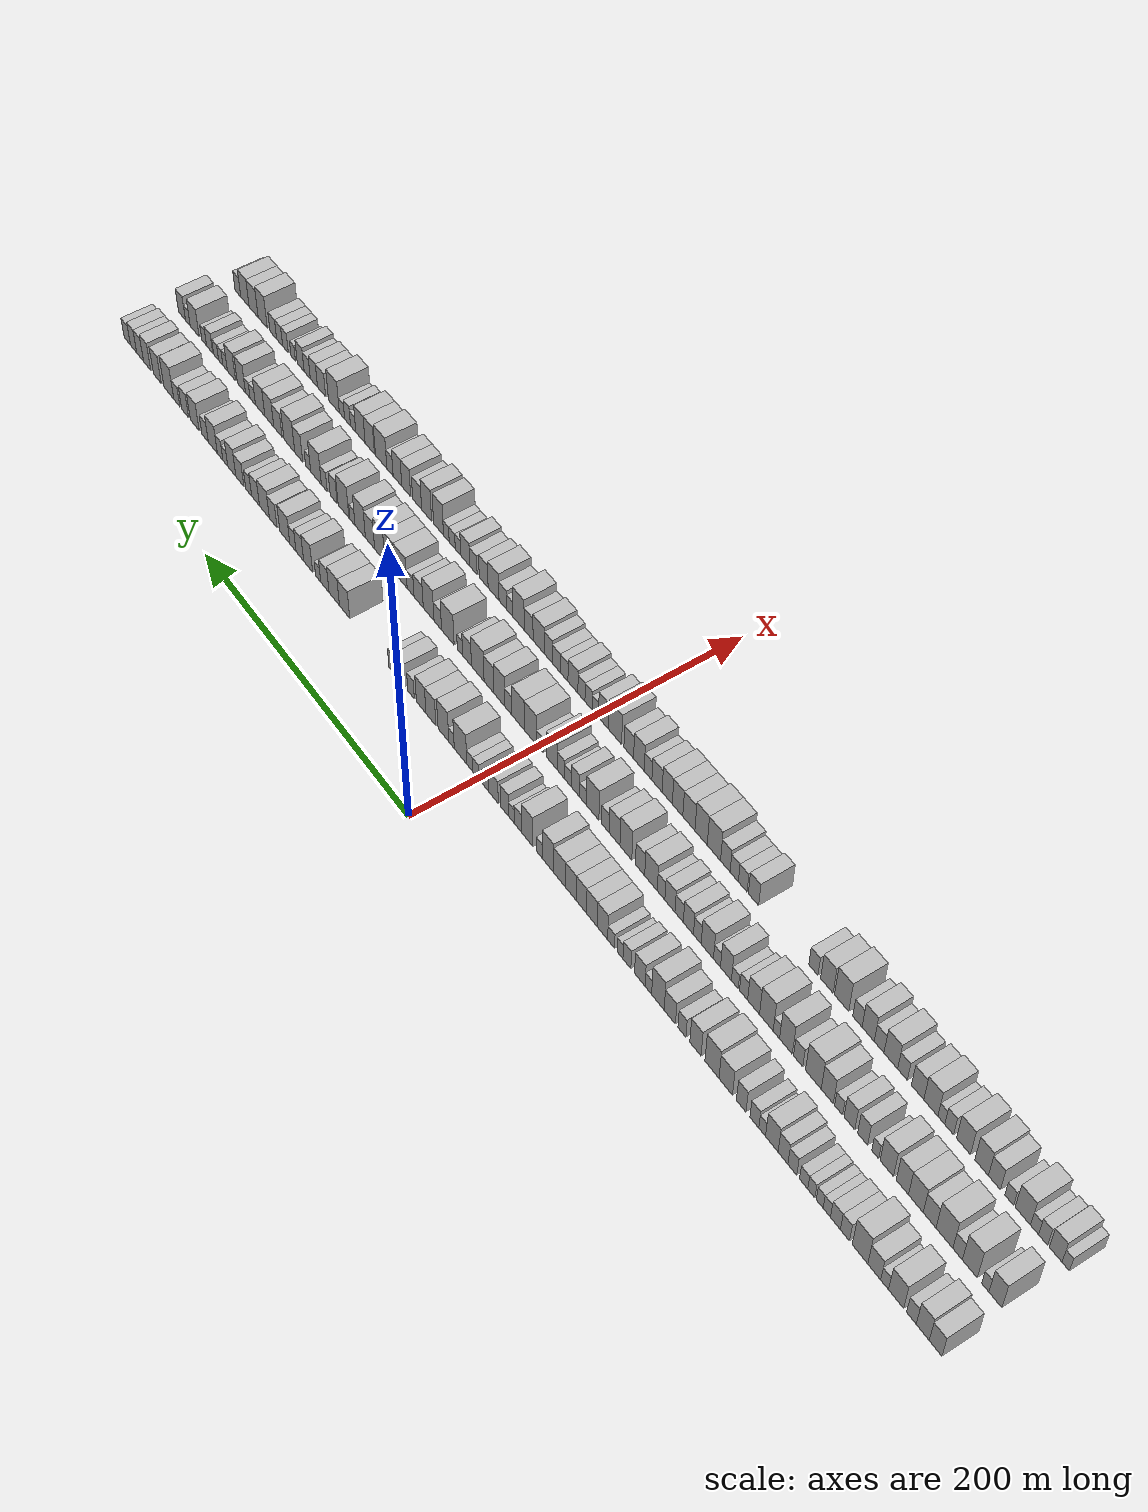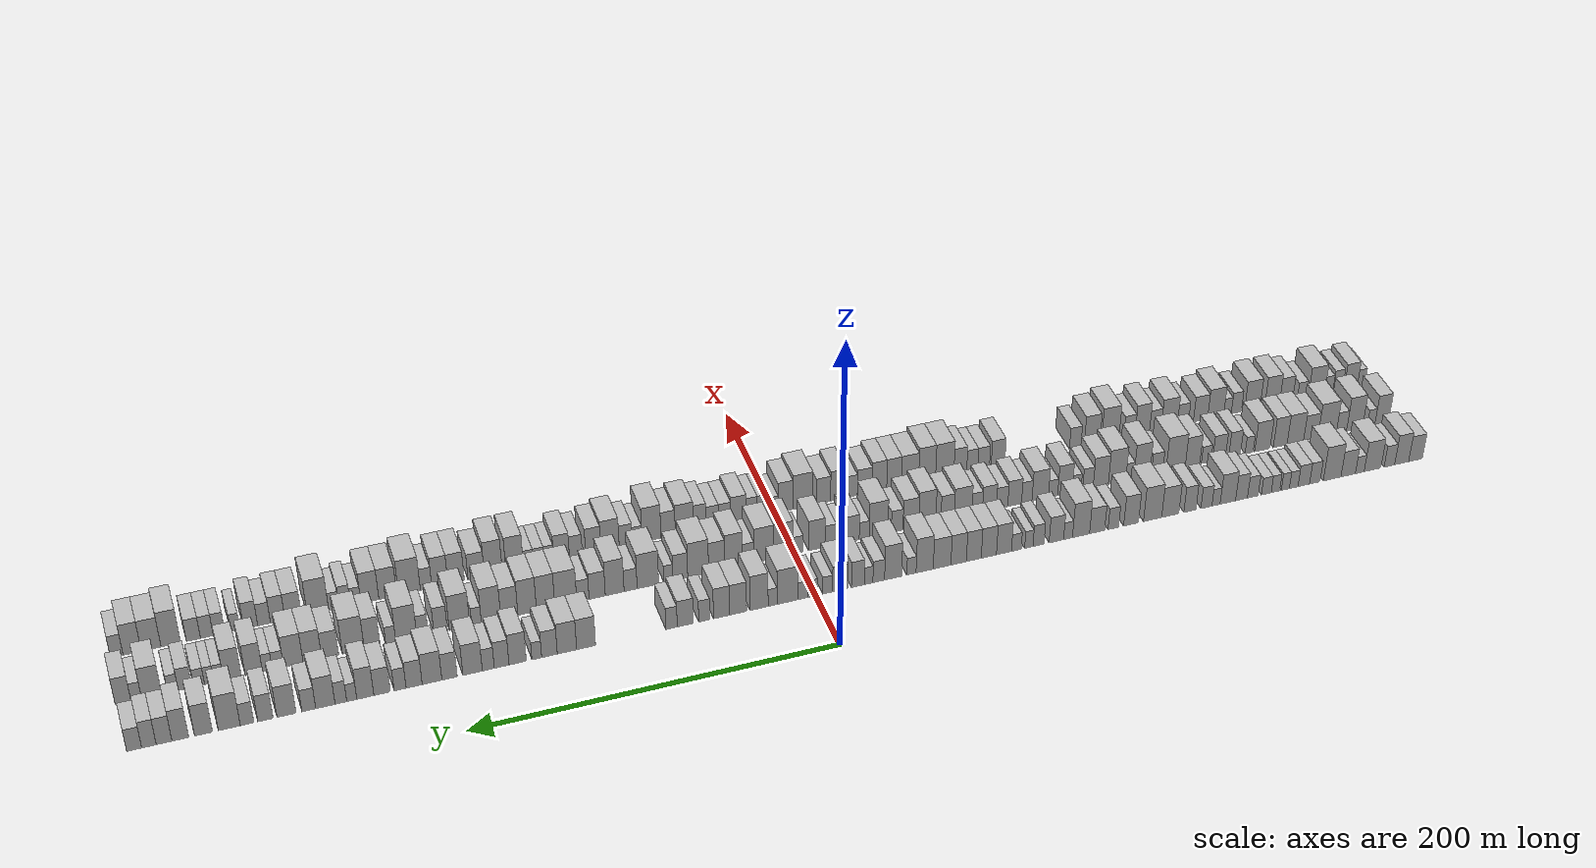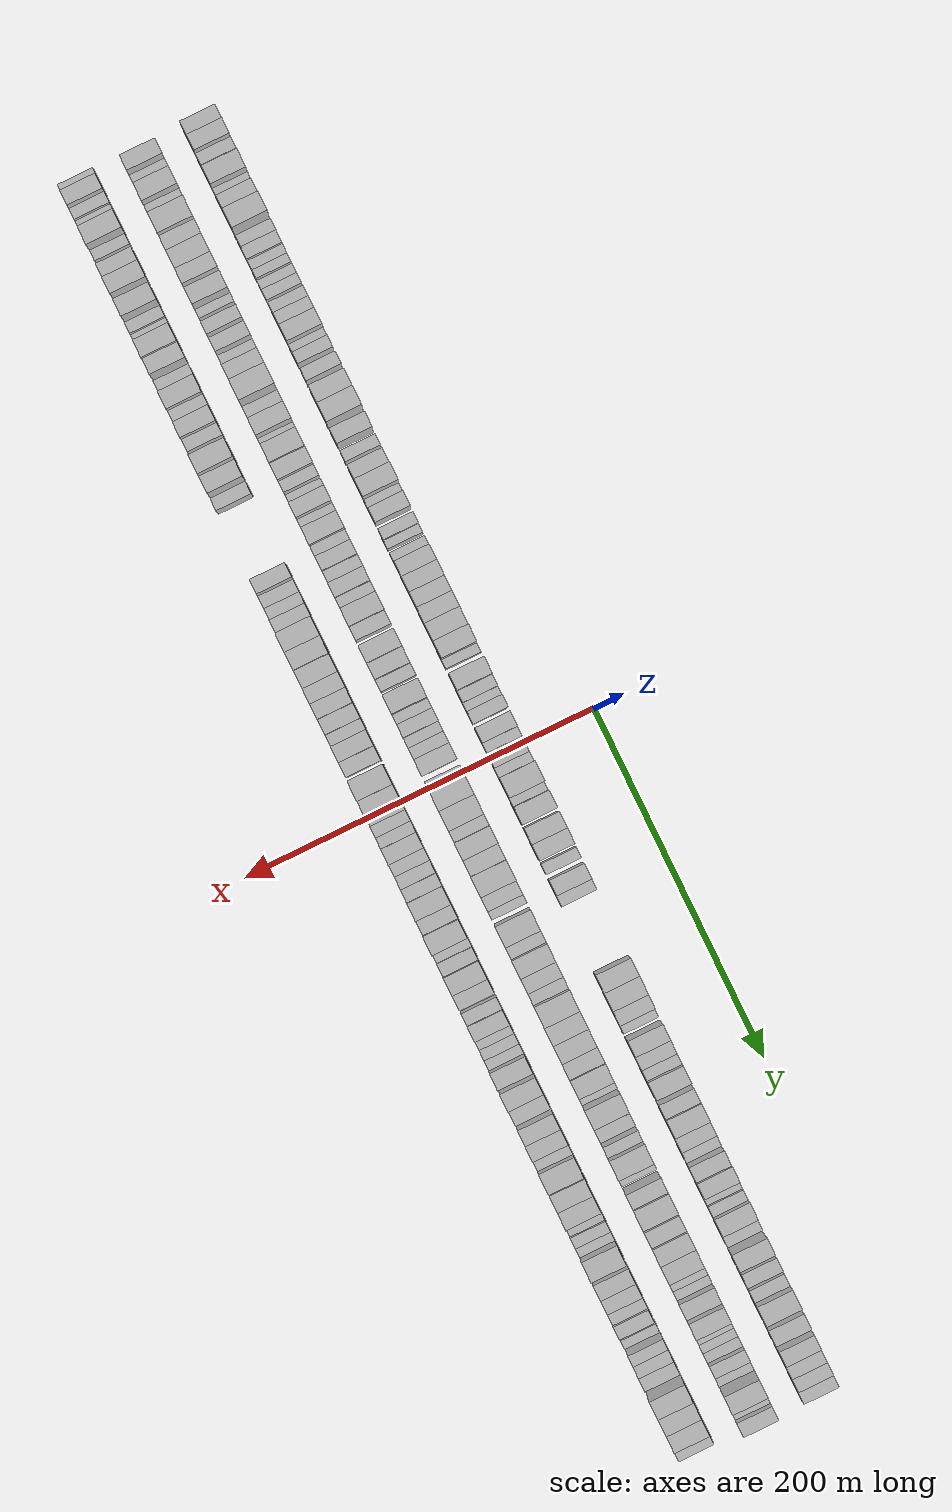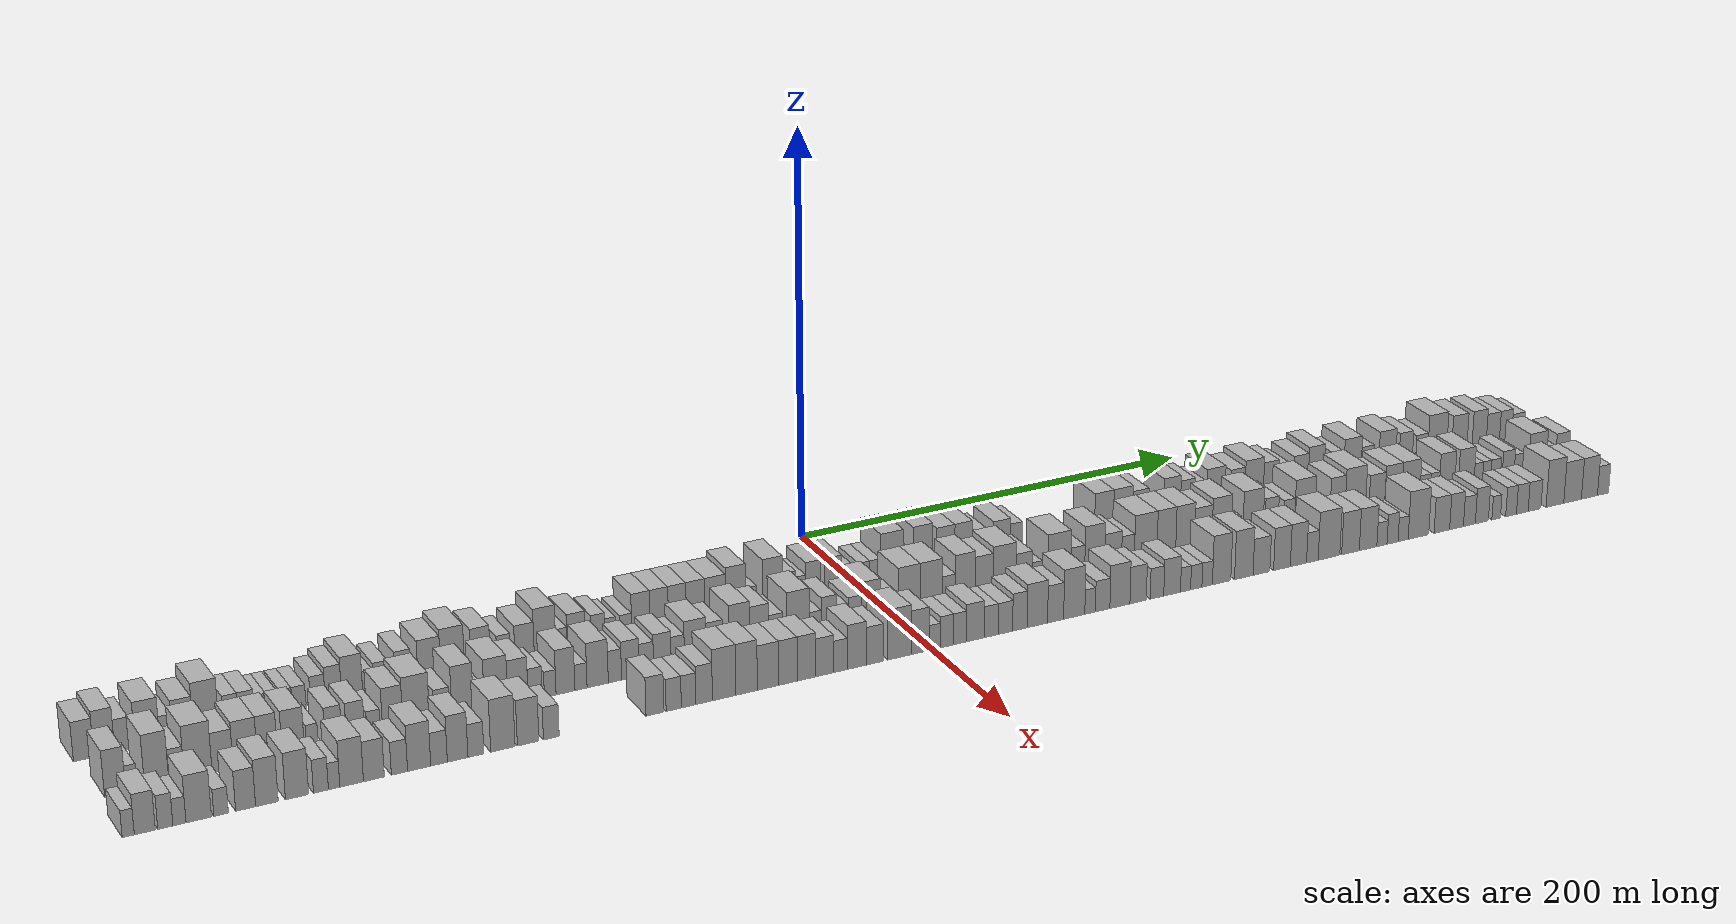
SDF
<sdf version="1.6">
 <world name="default">
  <scene>
   <sky><clouds><speed>12</speed></clouds></sky>
   <ambient>0.4 0.4 0.4 1</ambient>
   <background>0.7 0.7 0.7 1</background>
   <shadows>1</shadows>
  </scene>
  <gravity>0 0 -9.8066</gravity>
  <magnetic_field>6e-06 2.3e-05 -4.2e-05</magnetic_field>
  <physics default="0" name="default_physics" type="ode">
   <ode>
    <solver>
     <type>quick</type>
     <iters>10</iters>
     <sor>1.0</sor>
     <use_dynamic_moi_rescaling>0</use_dynamic_moi_rescaling>
    </solver>
    <constraints>
     <cfm>0</cfm>
     <erp>0.2</erp>
     <contact_max_correcting_vel>100</contact_max_correcting_vel>
     <contact_surface_layer>0.001</contact_surface_layer>
    </constraints>
   </ode>
   <max_step_size>0.004</max_step_size>
   <real_time_factor>1</real_time_factor>
   <real_time_update_rate>250</real_time_update_rate>
  </physics>
  <light name="sun" type="directional">
   <pose>0 0 10 0 0 0</pose>
   <diffuse>0.8 0.8 0.8 1</diffuse>
   <specular>0.2 0.2 0.2 1</specular>
   <attenuation>
    <range>1000</range>
    <constant>0.9</constant>
    <linear>0.01</linear>
    <quadratic>0.001</quadratic>
   </attenuation>
   <direction>-0.5 0.1 -0.9</direction>
  </light>
  <model name="building_1">
   <static>1</static>
   <pose>50.0000 -355.7108 0 0.000000 0.000000 0.000000</pose>
   <link name="link">
    <pose>0 0 9.00 0 0 0</pose>
    <collision name="collision"><geometry><box><size>20.0000 8.5783 18.0000</size></box></geometry></collision>
    <visual name="visual">
     <cast_shadows>0</cast_shadows>
     <geometry><box><size>20.0000 8.5783 18.0000</size></box></geometry>
     <material>
      <script>
       <uri>model://HANNAS_wall/materials/scripts</uri>
       <uri>model://HANNAS_wall/materials/textures</uri>
       <name>vrc/HANNAS_wall</name>
      </script>
     </material>
    </visual>
   </link>
  </model>
  <model name="building_2">
   <static>1</static>
   <pose>50.0000 -347.0402 0 0.000000 0.000000 0.000000</pose>
   <link name="link">
    <pose>0 0 10.50 0 0 0</pose>
    <collision name="collision"><geometry><box><size>20.0000 8.7629 21.0000</size></box></geometry></collision>
    <visual name="visual">
     <cast_shadows>0</cast_shadows>
     <geometry><box><size>20.0000 8.7629 21.0000</size></box></geometry>
     <material>
      <script>
       <uri>model://HANNAS_wall/materials/scripts</uri>
       <uri>model://HANNAS_wall/materials/textures</uri>
       <name>vrc/HANNAS_wall</name>
      </script>
     </material>
    </visual>
   </link>
  </model>
  <model name="building_3">
   <static>1</static>
   <pose>50.0000 -339.3646 0 0.000000 0.000000 0.000000</pose>
   <link name="link">
    <pose>0 0 7.50 0 0 0</pose>
    <collision name="collision"><geometry><box><size>20.0000 6.5883 15.0000</size></box></geometry></collision>
    <visual name="visual">
     <cast_shadows>0</cast_shadows>
     <geometry><box><size>20.0000 6.5883 15.0000</size></box></geometry>
     <material>
      <script>
       <uri>model://HANNAS_wall/materials/scripts</uri>
       <uri>model://HANNAS_wall/materials/textures</uri>
       <name>vrc/HANNAS_wall</name>
      </script>
     </material>
    </visual>
   </link>
  </model>
  <model name="building_4">
   <static>1</static>
   <pose>50.0000 -328.8616 0 0.000000 0.000000 0.000000</pose>
   <link name="link">
    <pose>0 0 10.50 0 0 0</pose>
    <collision name="collision"><geometry><box><size>20.0000 10.4178 21.0000</size></box></geometry></collision>
    <visual name="visual">
     <cast_shadows>0</cast_shadows>
     <geometry><box><size>20.0000 10.4178 21.0000</size></box></geometry>
     <material>
      <script>
       <uri>model://HANNAS_wall/materials/scripts</uri>
       <uri>model://HANNAS_wall/materials/textures</uri>
       <name>vrc/HANNAS_wall</name>
      </script>
     </material>
    </visual>
   </link>
  </model>
  <model name="building_5">
   <static>1</static>
   <pose>50.0000 -320.9417 0 0.000000 0.000000 0.000000</pose>
   <link name="link">
    <pose>0 0 6.00 0 0 0</pose>
    <collision name="collision"><geometry><box><size>20.0000 5.4220 12.0000</size></box></geometry></collision>
    <visual name="visual">
     <cast_shadows>0</cast_shadows>
     <geometry><box><size>20.0000 5.4220 12.0000</size></box></geometry>
     <material>
      <script>
       <uri>model://HANNAS_wall/materials/scripts</uri>
       <uri>model://HANNAS_wall/materials/textures</uri>
       <name>vrc/HANNAS_wall</name>
      </script>
     </material>
    </visual>
   </link>
  </model>
  <model name="building_6">
   <static>1</static>
   <pose>50.0000 -313.7510 0 0.000000 0.000000 0.000000</pose>
   <link name="link">
    <pose>0 0 9.00 0 0 0</pose>
    <collision name="collision"><geometry><box><size>20.0000 8.9593 18.0000</size></box></geometry></collision>
    <visual name="visual">
     <cast_shadows>0</cast_shadows>
     <geometry><box><size>20.0000 8.9593 18.0000</size></box></geometry>
     <material>
      <script>
       <uri>model://HANNAS_wall/materials/scripts</uri>
       <uri>model://HANNAS_wall/materials/textures</uri>
       <name>vrc/HANNAS_wall</name>
      </script>
     </material>
    </visual>
   </link>
  </model>
  <model name="building_7">
   <static>1</static>
   <pose>50.0000 -303.7959 0 0.000000 0.000000 0.000000</pose>
   <link name="link">
    <pose>0 0 12.00 0 0 0</pose>
    <collision name="collision"><geometry><box><size>20.0000 10.9510 24.0000</size></box></geometry></collision>
    <visual name="visual">
     <cast_shadows>0</cast_shadows>
     <geometry><box><size>20.0000 10.9510 24.0000</size></box></geometry>
     <material>
      <script>
       <uri>model://HANNAS_wall/materials/scripts</uri>
       <uri>model://HANNAS_wall/materials/textures</uri>
       <name>vrc/HANNAS_wall</name>
      </script>
     </material>
    </visual>
   </link>
  </model>
  <model name="building_8">
   <static>1</static>
   <pose>50.0000 -293.0944 0 0.000000 0.000000 0.000000</pose>
   <link name="link">
    <pose>0 0 7.50 0 0 0</pose>
    <collision name="collision"><geometry><box><size>20.0000 6.4519 15.0000</size></box></geometry></collision>
    <visual name="visual">
     <cast_shadows>0</cast_shadows>
     <geometry><box><size>20.0000 6.4519 15.0000</size></box></geometry>
     <material>
      <script>
       <uri>model://HANNAS_wall/materials/scripts</uri>
       <uri>model://HANNAS_wall/materials/textures</uri>
       <name>vrc/HANNAS_wall</name>
      </script>
     </material>
    </visual>
   </link>
  </model>
  <model name="building_9">
   <static>1</static>
   <pose>50.0000 -286.3283 0 0.000000 0.000000 0.000000</pose>
   <link name="link">
    <pose>0 0 7.50 0 0 0</pose>
    <collision name="collision"><geometry><box><size>20.0000 7.0803 15.0000</size></box></geometry></collision>
    <visual name="visual">
     <cast_shadows>0</cast_shadows>
     <geometry><box><size>20.0000 7.0803 15.0000</size></box></geometry>
     <material>
      <script>
       <uri>model://HANNAS_wall/materials/scripts</uri>
       <uri>model://HANNAS_wall/materials/textures</uri>
       <name>vrc/HANNAS_wall</name>
      </script>
     </material>
    </visual>
   </link>
  </model>
  <model name="building_10">
   <static>1</static>
   <pose>50.0000 -280.1579 0 0.000000 0.000000 0.000000</pose>
   <link name="link">
    <pose>0 0 6.00 0 0 0</pose>
    <collision name="collision"><geometry><box><size>20.0000 5.2603 12.0000</size></box></geometry></collision>
    <visual name="visual">
     <cast_shadows>0</cast_shadows>
     <geometry><box><size>20.0000 5.2603 12.0000</size></box></geometry>
     <material>
      <script>
       <uri>model://HANNAS_wall/materials/scripts</uri>
       <uri>model://HANNAS_wall/materials/textures</uri>
       <name>vrc/HANNAS_wall</name>
      </script>
     </material>
    </visual>
   </link>
  </model>
  <model name="building_11">
   <static>1</static>
   <pose>50.0000 -275.0595 0 0.000000 0.000000 0.000000</pose>
   <link name="link">
    <pose>0 0 6.00 0 0 0</pose>
    <collision name="collision"><geometry><box><size>20.0000 4.9366 12.0000</size></box></geometry></collision>
    <visual name="visual">
     <cast_shadows>0</cast_shadows>
     <geometry><box><size>20.0000 4.9366 12.0000</size></box></geometry>
     <material>
      <script>
       <uri>model://HANNAS_wall/materials/scripts</uri>
       <uri>model://HANNAS_wall/materials/textures</uri>
       <name>vrc/HANNAS_wall</name>
      </script>
     </material>
    </visual>
   </link>
  </model>
  <model name="building_12">
   <static>1</static>
   <pose>50.0000 -269.0004 0 0.000000 0.000000 0.000000</pose>
   <link name="link">
    <pose>0 0 6.00 0 0 0</pose>
    <collision name="collision"><geometry><box><size>20.0000 5.1815 12.0000</size></box></geometry></collision>
    <visual name="visual">
     <cast_shadows>0</cast_shadows>
     <geometry><box><size>20.0000 5.1815 12.0000</size></box></geometry>
     <material>
      <script>
       <uri>model://HANNAS_wall/materials/scripts</uri>
       <uri>model://HANNAS_wall/materials/textures</uri>
       <name>vrc/HANNAS_wall</name>
      </script>
     </material>
    </visual>
   </link>
  </model>
  <model name="building_13">
   <static>1</static>
   <pose>50.0000 -263.4154 0 0.000000 0.000000 0.000000</pose>
   <link name="link">
    <pose>0 0 6.00 0 0 0</pose>
    <collision name="collision"><geometry><box><size>20.0000 5.9884 12.0000</size></box></geometry></collision>
    <visual name="visual">
     <cast_shadows>0</cast_shadows>
     <geometry><box><size>20.0000 5.9884 12.0000</size></box></geometry>
     <material>
      <script>
       <uri>model://HANNAS_wall/materials/scripts</uri>
       <uri>model://HANNAS_wall/materials/textures</uri>
       <name>vrc/HANNAS_wall</name>
      </script>
     </material>
    </visual>
   </link>
  </model>
  <model name="building_14">
   <static>1</static>
   <pose>50.0000 -255.1728 0 0.000000 0.000000 0.000000</pose>
   <link name="link">
    <pose>0 0 7.50 0 0 0</pose>
    <collision name="collision"><geometry><box><size>20.0000 6.4968 15.0000</size></box></geometry></collision>
    <visual name="visual">
     <cast_shadows>0</cast_shadows>
     <geometry><box><size>20.0000 6.4968 15.0000</size></box></geometry>
     <material>
      <script>
       <uri>model://HANNAS_wall/materials/scripts</uri>
       <uri>model://HANNAS_wall/materials/textures</uri>
       <name>vrc/HANNAS_wall</name>
      </script>
     </material>
    </visual>
   </link>
  </model>
  <model name="building_15">
   <static>1</static>
   <pose>50.0000 -248.3059 0 0.000000 0.000000 0.000000</pose>
   <link name="link">
    <pose>0 0 9.00 0 0 0</pose>
    <collision name="collision"><geometry><box><size>20.0000 7.2370 18.0000</size></box></geometry></collision>
    <visual name="visual">
     <cast_shadows>0</cast_shadows>
     <geometry><box><size>20.0000 7.2370 18.0000</size></box></geometry>
     <material>
      <script>
       <uri>model://HANNAS_wall/materials/scripts</uri>
       <uri>model://HANNAS_wall/materials/textures</uri>
       <name>vrc/HANNAS_wall</name>
      </script>
     </material>
    </visual>
   </link>
  </model>
  <model name="building_16">
   <static>1</static>
   <pose>50.0000 -240.0128 0 0.000000 0.000000 0.000000</pose>
   <link name="link">
    <pose>0 0 10.50 0 0 0</pose>
    <collision name="collision"><geometry><box><size>20.0000 9.3492 21.0000</size></box></geometry></collision>
    <visual name="visual">
     <cast_shadows>0</cast_shadows>
     <geometry><box><size>20.0000 9.3492 21.0000</size></box></geometry>
     <material>
      <script>
       <uri>model://HANNAS_wall/materials/scripts</uri>
       <uri>model://HANNAS_wall/materials/textures</uri>
       <name>vrc/HANNAS_wall</name>
      </script>
     </material>
    </visual>
   </link>
  </model>
  <model name="building_17">
   <static>1</static>
   <pose>50.0000 -232.8654 0 0.000000 0.000000 0.000000</pose>
   <link name="link">
    <pose>0 0 6.00 0 0 0</pose>
    <collision name="collision"><geometry><box><size>20.0000 4.9455 12.0000</size></box></geometry></collision>
    <visual name="visual">
     <cast_shadows>0</cast_shadows>
     <geometry><box><size>20.0000 4.9455 12.0000</size></box></geometry>
     <material>
      <script>
       <uri>model://HANNAS_wall/materials/scripts</uri>
       <uri>model://HANNAS_wall/materials/textures</uri>
       <name>vrc/HANNAS_wall</name>
      </script>
     </material>
    </visual>
   </link>
  </model>
  <model name="building_18">
   <static>1</static>
   <pose>50.0000 -227.0547 0 0.000000 0.000000 0.000000</pose>
   <link name="link">
    <pose>0 0 7.50 0 0 0</pose>
    <collision name="collision"><geometry><box><size>20.0000 6.6760 15.0000</size></box></geometry></collision>
    <visual name="visual">
     <cast_shadows>0</cast_shadows>
     <geometry><box><size>20.0000 6.6760 15.0000</size></box></geometry>
     <material>
      <script>
       <uri>model://HANNAS_wall/materials/scripts</uri>
       <uri>model://HANNAS_wall/materials/textures</uri>
       <name>vrc/HANNAS_wall</name>
      </script>
     </material>
    </visual>
   </link>
  </model>
  <model name="building_19">
   <static>1</static>
   <pose>50.0000 -217.1015 0 0.000000 0.000000 0.000000</pose>
   <link name="link">
    <pose>0 0 9.00 0 0 0</pose>
    <collision name="collision"><geometry><box><size>20.0000 7.2303 18.0000</size></box></geometry></collision>
    <visual name="visual">
     <cast_shadows>0</cast_shadows>
     <geometry><box><size>20.0000 7.2303 18.0000</size></box></geometry>
     <material>
      <script>
       <uri>model://HANNAS_wall/materials/scripts</uri>
       <uri>model://HANNAS_wall/materials/textures</uri>
       <name>vrc/HANNAS_wall</name>
      </script>
     </material>
    </visual>
   </link>
  </model>
  <model name="building_20">
   <static>1</static>
   <pose>50.0000 -205.3397 0 0.000000 0.000000 0.000000</pose>
   <link name="link">
    <pose>0 0 10.50 0 0 0</pose>
    <collision name="collision"><geometry><box><size>20.0000 10.2934 21.0000</size></box></geometry></collision>
    <visual name="visual">
     <cast_shadows>0</cast_shadows>
     <geometry><box><size>20.0000 10.2934 21.0000</size></box></geometry>
     <material>
      <script>
       <uri>model://HANNAS_wall/materials/scripts</uri>
       <uri>model://HANNAS_wall/materials/textures</uri>
       <name>vrc/HANNAS_wall</name>
      </script>
     </material>
    </visual>
   </link>
  </model>
  <model name="building_21">
   <static>1</static>
   <pose>50.0000 -194.7656 0 0.000000 0.000000 0.000000</pose>
   <link name="link">
    <pose>0 0 12.00 0 0 0</pose>
    <collision name="collision"><geometry><box><size>20.0000 10.8548 24.0000</size></box></geometry></collision>
    <visual name="visual">
     <cast_shadows>0</cast_shadows>
     <geometry><box><size>20.0000 10.8548 24.0000</size></box></geometry>
     <material>
      <script>
       <uri>model://HANNAS_wall/materials/scripts</uri>
       <uri>model://HANNAS_wall/materials/textures</uri>
       <name>vrc/HANNAS_wall</name>
      </script>
     </material>
    </visual>
   </link>
  </model>
  <model name="building_22">
   <static>1</static>
   <pose>50.0000 -181.9417 0 0.000000 0.000000 0.000000</pose>
   <link name="link">
    <pose>0 0 10.50 0 0 0</pose>
    <collision name="collision"><geometry><box><size>20.0000 8.7929 21.0000</size></box></geometry></collision>
    <visual name="visual">
     <cast_shadows>0</cast_shadows>
     <geometry><box><size>20.0000 8.7929 21.0000</size></box></geometry>
     <material>
      <script>
       <uri>model://HANNAS_wall/materials/scripts</uri>
       <uri>model://HANNAS_wall/materials/textures</uri>
       <name>vrc/HANNAS_wall</name>
      </script>
     </material>
    </visual>
   </link>
  </model>
  <model name="building_23">
   <static>1</static>
   <pose>50.0000 -171.4032 0 0.000000 0.000000 0.000000</pose>
   <link name="link">
    <pose>0 0 7.50 0 0 0</pose>
    <collision name="collision"><geometry><box><size>20.0000 6.2841 15.0000</size></box></geometry></collision>
    <visual name="visual">
     <cast_shadows>0</cast_shadows>
     <geometry><box><size>20.0000 6.2841 15.0000</size></box></geometry>
     <material>
      <script>
       <uri>model://HANNAS_wall/materials/scripts</uri>
       <uri>model://HANNAS_wall/materials/textures</uri>
       <name>vrc/HANNAS_wall</name>
      </script>
     </material>
    </visual>
   </link>
  </model>
  <model name="building_24">
   <static>1</static>
   <pose>50.0000 -161.8031 0 0.000000 0.000000 0.000000</pose>
   <link name="link">
    <pose>0 0 9.00 0 0 0</pose>
    <collision name="collision"><geometry><box><size>20.0000 8.9161 18.0000</size></box></geometry></collision>
    <visual name="visual">
     <cast_shadows>0</cast_shadows>
     <geometry><box><size>20.0000 8.9161 18.0000</size></box></geometry>
     <material>
      <script>
       <uri>model://HANNAS_wall/materials/scripts</uri>
       <uri>model://HANNAS_wall/materials/textures</uri>
       <name>vrc/HANNAS_wall</name>
      </script>
     </material>
    </visual>
   </link>
  </model>
  <model name="building_25">
   <static>1</static>
   <pose>50.0000 -152.3166 0 0.000000 0.000000 0.000000</pose>
   <link name="link">
    <pose>0 0 12.00 0 0 0</pose>
    <collision name="collision"><geometry><box><size>20.0000 10.0570 24.0000</size></box></geometry></collision>
    <visual name="visual">
     <cast_shadows>0</cast_shadows>
     <geometry><box><size>20.0000 10.0570 24.0000</size></box></geometry>
     <material>
      <script>
       <uri>model://HANNAS_wall/materials/scripts</uri>
       <uri>model://HANNAS_wall/materials/textures</uri>
       <name>vrc/HANNAS_wall</name>
      </script>
     </material>
    </visual>
   </link>
  </model>
  <model name="building_26">
   <static>1</static>
   <pose>50.0000 -144.6645 0 0.000000 0.000000 0.000000</pose>
   <link name="link">
    <pose>0 0 6.00 0 0 0</pose>
    <collision name="collision"><geometry><box><size>20.0000 5.2472 12.0000</size></box></geometry></collision>
    <visual name="visual">
     <cast_shadows>0</cast_shadows>
     <geometry><box><size>20.0000 5.2472 12.0000</size></box></geometry>
     <material>
      <script>
       <uri>model://HANNAS_wall/materials/scripts</uri>
       <uri>model://HANNAS_wall/materials/textures</uri>
       <name>vrc/HANNAS_wall</name>
      </script>
     </material>
    </visual>
   </link>
  </model>
  <model name="building_27">
   <static>1</static>
   <pose>50.0000 -137.7980 0 0.000000 0.000000 0.000000</pose>
   <link name="link">
    <pose>0 0 9.00 0 0 0</pose>
    <collision name="collision"><geometry><box><size>20.0000 8.4859 18.0000</size></box></geometry></collision>
    <visual name="visual">
     <cast_shadows>0</cast_shadows>
     <geometry><box><size>20.0000 8.4859 18.0000</size></box></geometry>
     <material>
      <script>
       <uri>model://HANNAS_wall/materials/scripts</uri>
       <uri>model://HANNAS_wall/materials/textures</uri>
       <name>vrc/HANNAS_wall</name>
      </script>
     </material>
    </visual>
   </link>
  </model>
  <model name="building_28">
   <static>1</static>
   <pose>50.0000 -127.3299 0 0.000000 0.000000 0.000000</pose>
   <link name="link">
    <pose>0 0 7.50 0 0 0</pose>
    <collision name="collision"><geometry><box><size>20.0000 6.4503 15.0000</size></box></geometry></collision>
    <visual name="visual">
     <cast_shadows>0</cast_shadows>
     <geometry><box><size>20.0000 6.4503 15.0000</size></box></geometry>
     <material>
      <script>
       <uri>model://HANNAS_wall/materials/scripts</uri>
       <uri>model://HANNAS_wall/materials/textures</uri>
       <name>vrc/HANNAS_wall</name>
      </script>
     </material>
    </visual>
   </link>
  </model>
  <model name="building_29">
   <static>1</static>
   <pose>50.0000 -121.6723 0 0.000000 0.000000 0.000000</pose>
   <link name="link">
    <pose>0 0 6.00 0 0 0</pose>
    <collision name="collision"><geometry><box><size>20.0000 4.8649 12.0000</size></box></geometry></collision>
    <visual name="visual">
     <cast_shadows>0</cast_shadows>
     <geometry><box><size>20.0000 4.8649 12.0000</size></box></geometry>
     <material>
      <script>
       <uri>model://HANNAS_wall/materials/scripts</uri>
       <uri>model://HANNAS_wall/materials/textures</uri>
       <name>vrc/HANNAS_wall</name>
      </script>
     </material>
    </visual>
   </link>
  </model>
  <model name="building_30">
   <static>1</static>
   <pose>50.0000 -114.3965 0 0.000000 0.000000 0.000000</pose>
   <link name="link">
    <pose>0 0 6.00 0 0 0</pose>
    <collision name="collision"><geometry><box><size>20.0000 5.6867 12.0000</size></box></geometry></collision>
    <visual name="visual">
     <cast_shadows>0</cast_shadows>
     <geometry><box><size>20.0000 5.6867 12.0000</size></box></geometry>
     <material>
      <script>
       <uri>model://HANNAS_wall/materials/scripts</uri>
       <uri>model://HANNAS_wall/materials/textures</uri>
       <name>vrc/HANNAS_wall</name>
      </script>
     </material>
    </visual>
   </link>
  </model>
  <model name="building_31">
   <static>1</static>
   <pose>50.0000 -107.1871 0 0.000000 0.000000 0.000000</pose>
   <link name="link">
    <pose>0 0 10.50 0 0 0</pose>
    <collision name="collision"><geometry><box><size>20.0000 8.7320 21.0000</size></box></geometry></collision>
    <visual name="visual">
     <cast_shadows>0</cast_shadows>
     <geometry><box><size>20.0000 8.7320 21.0000</size></box></geometry>
     <material>
      <script>
       <uri>model://HANNAS_wall/materials/scripts</uri>
       <uri>model://HANNAS_wall/materials/textures</uri>
       <name>vrc/HANNAS_wall</name>
      </script>
     </material>
    </visual>
   </link>
  </model>
  <model name="building_32">
   <static>1</static>
   <pose>50.0000 -98.4116 0 0.000000 0.000000 0.000000</pose>
   <link name="link">
    <pose>0 0 10.50 0 0 0</pose>
    <collision name="collision"><geometry><box><size>20.0000 8.8189 21.0000</size></box></geometry></collision>
    <visual name="visual">
     <cast_shadows>0</cast_shadows>
     <geometry><box><size>20.0000 8.8189 21.0000</size></box></geometry>
     <material>
      <script>
       <uri>model://HANNAS_wall/materials/scripts</uri>
       <uri>model://HANNAS_wall/materials/textures</uri>
       <name>vrc/HANNAS_wall</name>
      </script>
     </material>
    </visual>
   </link>
  </model>
  <model name="building_33">
   <static>1</static>
   <pose>50.0000 -89.6995 0 0.000000 0.000000 0.000000</pose>
   <link name="link">
    <pose>0 0 10.50 0 0 0</pose>
    <collision name="collision"><geometry><box><size>20.0000 8.6054 21.0000</size></box></geometry></collision>
    <visual name="visual">
     <cast_shadows>0</cast_shadows>
     <geometry><box><size>20.0000 8.6054 21.0000</size></box></geometry>
     <material>
      <script>
       <uri>model://HANNAS_wall/materials/scripts</uri>
       <uri>model://HANNAS_wall/materials/textures</uri>
       <name>vrc/HANNAS_wall</name>
      </script>
     </material>
    </visual>
   </link>
  </model>
  <model name="building_34">
   <static>1</static>
   <pose>50.0000 -80.9385 0 0.000000 0.000000 0.000000</pose>
   <link name="link">
    <pose>0 0 10.50 0 0 0</pose>
    <collision name="collision"><geometry><box><size>20.0000 8.9166 21.0000</size></box></geometry></collision>
    <visual name="visual">
     <cast_shadows>0</cast_shadows>
     <geometry><box><size>20.0000 8.9166 21.0000</size></box></geometry>
     <material>
      <script>
       <uri>model://HANNAS_wall/materials/scripts</uri>
       <uri>model://HANNAS_wall/materials/textures</uri>
       <name>vrc/HANNAS_wall</name>
      </script>
     </material>
    </visual>
   </link>
  </model>
  <model name="building_35">
   <static>1</static>
   <pose>50.0000 -71.4100 0 0.000000 0.000000 0.000000</pose>
   <link name="link">
    <pose>0 0 10.50 0 0 0</pose>
    <collision name="collision"><geometry><box><size>20.0000 10.1404 21.0000</size></box></geometry></collision>
    <visual name="visual">
     <cast_shadows>0</cast_shadows>
     <geometry><box><size>20.0000 10.1404 21.0000</size></box></geometry>
     <material>
      <script>
       <uri>model://HANNAS_wall/materials/scripts</uri>
       <uri>model://HANNAS_wall/materials/textures</uri>
       <name>vrc/HANNAS_wall</name>
      </script>
     </material>
    </visual>
   </link>
  </model>
  <model name="building_36">
   <static>1</static>
   <pose>50.0000 -61.4313 0 0.000000 0.000000 0.000000</pose>
   <link name="link">
    <pose>0 0 12.00 0 0 0</pose>
    <collision name="collision"><geometry><box><size>20.0000 9.8170 24.0000</size></box></geometry></collision>
    <visual name="visual">
     <cast_shadows>0</cast_shadows>
     <geometry><box><size>20.0000 9.8170 24.0000</size></box></geometry>
     <material>
      <script>
       <uri>model://HANNAS_wall/materials/scripts</uri>
       <uri>model://HANNAS_wall/materials/textures</uri>
       <name>vrc/HANNAS_wall</name>
      </script>
     </material>
    </visual>
   </link>
  </model>
  <model name="building_37">
   <static>1</static>
   <pose>50.0000 -53.8903 0 0.000000 0.000000 0.000000</pose>
   <link name="link">
    <pose>0 0 6.00 0 0 0</pose>
    <collision name="collision"><geometry><box><size>20.0000 5.2652 12.0000</size></box></geometry></collision>
    <visual name="visual">
     <cast_shadows>0</cast_shadows>
     <geometry><box><size>20.0000 5.2652 12.0000</size></box></geometry>
     <material>
      <script>
       <uri>model://HANNAS_wall/materials/scripts</uri>
       <uri>model://HANNAS_wall/materials/textures</uri>
       <name>vrc/HANNAS_wall</name>
      </script>
     </material>
    </visual>
   </link>
  </model>
  <model name="building_38">
   <static>1</static>
   <pose>50.0000 -43.4119 0 0.000000 0.000000 0.000000</pose>
   <link name="link">
    <pose>0 0 12.00 0 0 0</pose>
    <collision name="collision"><geometry><box><size>20.0000 9.6916 24.0000</size></box></geometry></collision>
    <visual name="visual">
     <cast_shadows>0</cast_shadows>
     <geometry><box><size>20.0000 9.6916 24.0000</size></box></geometry>
     <material>
      <script>
       <uri>model://HANNAS_wall/materials/scripts</uri>
       <uri>model://HANNAS_wall/materials/textures</uri>
       <name>vrc/HANNAS_wall</name>
      </script>
     </material>
    </visual>
   </link>
  </model>
  <model name="building_39">
   <static>1</static>
   <pose>50.0000 -35.2519 0 0.000000 0.000000 0.000000</pose>
   <link name="link">
    <pose>0 0 7.50 0 0 0</pose>
    <collision name="collision"><geometry><box><size>20.0000 6.6284 15.0000</size></box></geometry></collision>
    <visual name="visual">
     <cast_shadows>0</cast_shadows>
     <geometry><box><size>20.0000 6.6284 15.0000</size></box></geometry>
     <material>
      <script>
       <uri>model://HANNAS_wall/materials/scripts</uri>
       <uri>model://HANNAS_wall/materials/textures</uri>
       <name>vrc/HANNAS_wall</name>
      </script>
     </material>
    </visual>
   </link>
  </model>
  <model name="building_40">
   <static>1</static>
   <pose>50.0000 -29.4817 0 0.000000 0.000000 0.000000</pose>
   <link name="link">
    <pose>0 0 6.00 0 0 0</pose>
    <collision name="collision"><geometry><box><size>20.0000 4.9120 12.0000</size></box></geometry></collision>
    <visual name="visual">
     <cast_shadows>0</cast_shadows>
     <geometry><box><size>20.0000 4.9120 12.0000</size></box></geometry>
     <material>
      <script>
       <uri>model://HANNAS_wall/materials/scripts</uri>
       <uri>model://HANNAS_wall/materials/textures</uri>
       <name>vrc/HANNAS_wall</name>
      </script>
     </material>
    </visual>
   </link>
  </model>
  <model name="building_41">
   <static>1</static>
   <pose>50.0000 -23.4032 0 0.000000 0.000000 0.000000</pose>
   <link name="link">
    <pose>0 0 9.00 0 0 0</pose>
    <collision name="collision"><geometry><box><size>20.0000 7.2448 18.0000</size></box></geometry></collision>
    <visual name="visual">
     <cast_shadows>0</cast_shadows>
     <geometry><box><size>20.0000 7.2448 18.0000</size></box></geometry>
     <material>
      <script>
       <uri>model://HANNAS_wall/materials/scripts</uri>
       <uri>model://HANNAS_wall/materials/textures</uri>
       <name>vrc/HANNAS_wall</name>
      </script>
     </material>
    </visual>
   </link>
  </model>
  <model name="building_42">
   <static>1</static>
   <pose>50.0000 -13.4413 0 0.000000 0.000000 0.000000</pose>
   <link name="link">
    <pose>0 0 9.00 0 0 0</pose>
    <collision name="collision"><geometry><box><size>20.0000 8.6791 18.0000</size></box></geometry></collision>
    <visual name="visual">
     <cast_shadows>0</cast_shadows>
     <geometry><box><size>20.0000 8.6791 18.0000</size></box></geometry>
     <material>
      <script>
       <uri>model://HANNAS_wall/materials/scripts</uri>
       <uri>model://HANNAS_wall/materials/textures</uri>
       <name>vrc/HANNAS_wall</name>
      </script>
     </material>
    </visual>
   </link>
  </model>
  <model name="building_43">
   <static>1</static>
   <pose>50.0000 -6.3569 0 0.000000 0.000000 0.000000</pose>
   <link name="link">
    <pose>0 0 6.00 0 0 0</pose>
    <collision name="collision"><geometry><box><size>20.0000 5.4895 12.0000</size></box></geometry></collision>
    <visual name="visual">
     <cast_shadows>0</cast_shadows>
     <geometry><box><size>20.0000 5.4895 12.0000</size></box></geometry>
     <material>
      <script>
       <uri>model://HANNAS_wall/materials/scripts</uri>
       <uri>model://HANNAS_wall/materials/textures</uri>
       <name>vrc/HANNAS_wall</name>
      </script>
     </material>
    </visual>
   </link>
  </model>
  <model name="building_44">
   <static>1</static>
   <pose>50.0000 2.2003 0 0.000000 0.000000 0.000000</pose>
   <link name="link">
    <pose>0 0 6.00 0 0 0</pose>
    <collision name="collision"><geometry><box><size>20.0000 5.6250 12.0000</size></box></geometry></collision>
    <visual name="visual">
     <cast_shadows>0</cast_shadows>
     <geometry><box><size>20.0000 5.6250 12.0000</size></box></geometry>
     <material>
      <script>
       <uri>model://HANNAS_wall/materials/scripts</uri>
       <uri>model://HANNAS_wall/materials/textures</uri>
       <name>vrc/HANNAS_wall</name>
      </script>
     </material>
    </visual>
   </link>
  </model>
  <model name="building_45">
   <static>1</static>
   <pose>50.0000 7.7510 0 0.000000 0.000000 0.000000</pose>
   <link name="link">
    <pose>0 0 6.00 0 0 0</pose>
    <collision name="collision"><geometry><box><size>20.0000 5.4763 12.0000</size></box></geometry></collision>
    <visual name="visual">
     <cast_shadows>0</cast_shadows>
     <geometry><box><size>20.0000 5.4763 12.0000</size></box></geometry>
     <material>
      <script>
       <uri>model://HANNAS_wall/materials/scripts</uri>
       <uri>model://HANNAS_wall/materials/textures</uri>
       <name>vrc/HANNAS_wall</name>
      </script>
     </material>
    </visual>
   </link>
  </model>
  <model name="building_46">
   <static>1</static>
   <pose>50.0000 16.2468 0 0.000000 0.000000 0.000000</pose>
   <link name="link">
    <pose>0 0 12.00 0 0 0</pose>
    <collision name="collision"><geometry><box><size>20.0000 11.5153 24.0000</size></box></geometry></collision>
    <visual name="visual">
     <cast_shadows>0</cast_shadows>
     <geometry><box><size>20.0000 11.5153 24.0000</size></box></geometry>
     <material>
      <script>
       <uri>model://HANNAS_wall/materials/scripts</uri>
       <uri>model://HANNAS_wall/materials/textures</uri>
       <name>vrc/HANNAS_wall</name>
      </script>
     </material>
    </visual>
   </link>
  </model>
  <model name="building_47">
   <static>1</static>
   <pose>50.0000 24.4752 0 0.000000 0.000000 0.000000</pose>
   <link name="link">
    <pose>0 0 6.00 0 0 0</pose>
    <collision name="collision"><geometry><box><size>20.0000 4.9416 12.0000</size></box></geometry></collision>
    <visual name="visual">
     <cast_shadows>0</cast_shadows>
     <geometry><box><size>20.0000 4.9416 12.0000</size></box></geometry>
     <material>
      <script>
       <uri>model://HANNAS_wall/materials/scripts</uri>
       <uri>model://HANNAS_wall/materials/textures</uri>
       <name>vrc/HANNAS_wall</name>
      </script>
     </material>
    </visual>
   </link>
  </model>
  <model name="building_48">
   <static>1</static>
   <pose>50.0000 31.9420 0 0.000000 0.000000 0.000000</pose>
   <link name="link">
    <pose>0 0 12.00 0 0 0</pose>
    <collision name="collision"><geometry><box><size>20.0000 9.9919 24.0000</size></box></geometry></collision>
    <visual name="visual">
     <cast_shadows>0</cast_shadows>
     <geometry><box><size>20.0000 9.9919 24.0000</size></box></geometry>
     <material>
      <script>
       <uri>model://HANNAS_wall/materials/scripts</uri>
       <uri>model://HANNAS_wall/materials/textures</uri>
       <name>vrc/HANNAS_wall</name>
      </script>
     </material>
    </visual>
   </link>
  </model>
  <model name="building_49">
   <static>1</static>
   <pose>50.0000 43.5863 0 0.000000 0.000000 0.000000</pose>
   <link name="link">
    <pose>0 0 10.50 0 0 0</pose>
    <collision name="collision"><geometry><box><size>20.0000 9.2966 21.0000</size></box></geometry></collision>
    <visual name="visual">
     <cast_shadows>0</cast_shadows>
     <geometry><box><size>20.0000 9.2966 21.0000</size></box></geometry>
     <material>
      <script>
       <uri>model://HANNAS_wall/materials/scripts</uri>
       <uri>model://HANNAS_wall/materials/textures</uri>
       <name>vrc/HANNAS_wall</name>
      </script>
     </material>
    </visual>
   </link>
  </model>
  <model name="building_50">
   <static>1</static>
   <pose>50.0000 52.7178 0 0.000000 0.000000 0.000000</pose>
   <link name="link">
    <pose>0 0 10.50 0 0 0</pose>
    <collision name="collision"><geometry><box><size>20.0000 8.9664 21.0000</size></box></geometry></collision>
    <visual name="visual">
     <cast_shadows>0</cast_shadows>
     <geometry><box><size>20.0000 8.9664 21.0000</size></box></geometry>
     <material>
      <script>
       <uri>model://HANNAS_wall/materials/scripts</uri>
       <uri>model://HANNAS_wall/materials/textures</uri>
       <name>vrc/HANNAS_wall</name>
      </script>
     </material>
    </visual>
   </link>
  </model>
  <model name="building_51">
   <static>1</static>
   <pose>50.0000 62.2641 0 0.000000 0.000000 0.000000</pose>
   <link name="link">
    <pose>0 0 7.50 0 0 0</pose>
    <collision name="collision"><geometry><box><size>20.0000 6.1261 15.0000</size></box></geometry></collision>
    <visual name="visual">
     <cast_shadows>0</cast_shadows>
     <geometry><box><size>20.0000 6.1261 15.0000</size></box></geometry>
     <material>
      <script>
       <uri>model://HANNAS_wall/materials/scripts</uri>
       <uri>model://HANNAS_wall/materials/textures</uri>
       <name>vrc/HANNAS_wall</name>
      </script>
     </material>
    </visual>
   </link>
  </model>
  <model name="building_52">
   <static>1</static>
   <pose>50.0000 72.7436 0 0.000000 0.000000 0.000000</pose>
   <link name="link">
    <pose>0 0 9.00 0 0 0</pose>
    <collision name="collision"><geometry><box><size>20.0000 8.8330 18.0000</size></box></geometry></collision>
    <visual name="visual">
     <cast_shadows>0</cast_shadows>
     <geometry><box><size>20.0000 8.8330 18.0000</size></box></geometry>
     <material>
      <script>
       <uri>model://HANNAS_wall/materials/scripts</uri>
       <uri>model://HANNAS_wall/materials/textures</uri>
       <name>vrc/HANNAS_wall</name>
      </script>
     </material>
    </visual>
   </link>
  </model>
  <model name="building_53">
   <static>1</static>
   <pose>50.0000 80.2752 0 0.000000 0.000000 0.000000</pose>
   <link name="link">
    <pose>0 0 7.50 0 0 0</pose>
    <collision name="collision"><geometry><box><size>20.0000 6.2301 15.0000</size></box></geometry></collision>
    <visual name="visual">
     <cast_shadows>0</cast_shadows>
     <geometry><box><size>20.0000 6.2301 15.0000</size></box></geometry>
     <material>
      <script>
       <uri>model://HANNAS_wall/materials/scripts</uri>
       <uri>model://HANNAS_wall/materials/textures</uri>
       <name>vrc/HANNAS_wall</name>
      </script>
     </material>
    </visual>
   </link>
  </model>
  <model name="building_54">
   <static>1</static>
   <pose>50.0000 126.6879 0 0.000000 0.000000 0.000000</pose>
   <link name="link">
    <pose>0 0 10.50 0 0 0</pose>
    <collision name="collision"><geometry><box><size>20.0000 10.1985 21.0000</size></box></geometry></collision>
    <visual name="visual">
     <cast_shadows>0</cast_shadows>
     <geometry><box><size>20.0000 10.1985 21.0000</size></box></geometry>
     <material>
      <script>
       <uri>model://HANNAS_wall/materials/scripts</uri>
       <uri>model://HANNAS_wall/materials/textures</uri>
       <name>vrc/HANNAS_wall</name>
      </script>
     </material>
    </visual>
   </link>
  </model>
  <model name="building_55">
   <static>1</static>
   <pose>50.0000 136.9837 0 0.000000 0.000000 0.000000</pose>
   <link name="link">
    <pose>0 0 10.50 0 0 0</pose>
    <collision name="collision"><geometry><box><size>20.0000 10.3931 21.0000</size></box></geometry></collision>
    <visual name="visual">
     <cast_shadows>0</cast_shadows>
     <geometry><box><size>20.0000 10.3931 21.0000</size></box></geometry>
     <material>
      <script>
       <uri>model://HANNAS_wall/materials/scripts</uri>
       <uri>model://HANNAS_wall/materials/textures</uri>
       <name>vrc/HANNAS_wall</name>
      </script>
     </material>
    </visual>
   </link>
  </model>
  <model name="building_56">
   <static>1</static>
   <pose>50.0000 146.3656 0 0.000000 0.000000 0.000000</pose>
   <link name="link">
    <pose>0 0 9.00 0 0 0</pose>
    <collision name="collision"><geometry><box><size>20.0000 8.3706 18.0000</size></box></geometry></collision>
    <visual name="visual">
     <cast_shadows>0</cast_shadows>
     <geometry><box><size>20.0000 8.3706 18.0000</size></box></geometry>
     <material>
      <script>
       <uri>model://HANNAS_wall/materials/scripts</uri>
       <uri>model://HANNAS_wall/materials/textures</uri>
       <name>vrc/HANNAS_wall</name>
      </script>
     </material>
    </visual>
   </link>
  </model>
  <model name="building_57">
   <static>1</static>
   <pose>50.0000 153.1683 0 0.000000 0.000000 0.000000</pose>
   <link name="link">
    <pose>0 0 6.00 0 0 0</pose>
    <collision name="collision"><geometry><box><size>20.0000 5.2348 12.0000</size></box></geometry></collision>
    <visual name="visual">
     <cast_shadows>0</cast_shadows>
     <geometry><box><size>20.0000 5.2348 12.0000</size></box></geometry>
     <material>
      <script>
       <uri>model://HANNAS_wall/materials/scripts</uri>
       <uri>model://HANNAS_wall/materials/textures</uri>
       <name>vrc/HANNAS_wall</name>
      </script>
     </material>
    </visual>
   </link>
  </model>
  <model name="building_58">
   <static>1</static>
   <pose>50.0000 163.3653 0 0.000000 0.000000 0.000000</pose>
   <link name="link">
    <pose>0 0 10.50 0 0 0</pose>
    <collision name="collision"><geometry><box><size>20.0000 9.1591 21.0000</size></box></geometry></collision>
    <visual name="visual">
     <cast_shadows>0</cast_shadows>
     <geometry><box><size>20.0000 9.1591 21.0000</size></box></geometry>
     <material>
      <script>
       <uri>model://HANNAS_wall/materials/scripts</uri>
       <uri>model://HANNAS_wall/materials/textures</uri>
       <name>vrc/HANNAS_wall</name>
      </script>
     </material>
    </visual>
   </link>
  </model>
  <model name="building_59">
   <static>1</static>
   <pose>50.0000 171.8690 0 0.000000 0.000000 0.000000</pose>
   <link name="link">
    <pose>0 0 9.00 0 0 0</pose>
    <collision name="collision"><geometry><box><size>20.0000 7.8484 18.0000</size></box></geometry></collision>
    <visual name="visual">
     <cast_shadows>0</cast_shadows>
     <geometry><box><size>20.0000 7.8484 18.0000</size></box></geometry>
     <material>
      <script>
       <uri>model://HANNAS_wall/materials/scripts</uri>
       <uri>model://HANNAS_wall/materials/textures</uri>
       <name>vrc/HANNAS_wall</name>
      </script>
     </material>
    </visual>
   </link>
  </model>
  <model name="building_60">
   <static>1</static>
   <pose>50.0000 178.9690 0 0.000000 0.000000 0.000000</pose>
   <link name="link">
    <pose>0 0 7.50 0 0 0</pose>
    <collision name="collision"><geometry><box><size>20.0000 6.3515 15.0000</size></box></geometry></collision>
    <visual name="visual">
     <cast_shadows>0</cast_shadows>
     <geometry><box><size>20.0000 6.3515 15.0000</size></box></geometry>
     <material>
      <script>
       <uri>model://HANNAS_wall/materials/scripts</uri>
       <uri>model://HANNAS_wall/materials/textures</uri>
       <name>vrc/HANNAS_wall</name>
      </script>
     </material>
    </visual>
   </link>
  </model>
  <model name="building_61">
   <static>1</static>
   <pose>50.0000 187.2679 0 0.000000 0.000000 0.000000</pose>
   <link name="link">
    <pose>0 0 10.50 0 0 0</pose>
    <collision name="collision"><geometry><box><size>20.0000 10.2464 21.0000</size></box></geometry></collision>
    <visual name="visual">
     <cast_shadows>0</cast_shadows>
     <geometry><box><size>20.0000 10.2464 21.0000</size></box></geometry>
     <material>
      <script>
       <uri>model://HANNAS_wall/materials/scripts</uri>
       <uri>model://HANNAS_wall/materials/textures</uri>
       <name>vrc/HANNAS_wall</name>
      </script>
     </material>
    </visual>
   </link>
  </model>
  <model name="building_62">
   <static>1</static>
   <pose>50.0000 199.4339 0 0.000000 0.000000 0.000000</pose>
   <link name="link">
    <pose>0 0 9.00 0 0 0</pose>
    <collision name="collision"><geometry><box><size>20.0000 8.0856 18.0000</size></box></geometry></collision>
    <visual name="visual">
     <cast_shadows>0</cast_shadows>
     <geometry><box><size>20.0000 8.0856 18.0000</size></box></geometry>
     <material>
      <script>
       <uri>model://HANNAS_wall/materials/scripts</uri>
       <uri>model://HANNAS_wall/materials/textures</uri>
       <name>vrc/HANNAS_wall</name>
      </script>
     </material>
    </visual>
   </link>
  </model>
  <model name="building_63">
   <static>1</static>
   <pose>50.0000 208.6387 0 0.000000 0.000000 0.000000</pose>
   <link name="link">
    <pose>0 0 10.50 0 0 0</pose>
    <collision name="collision"><geometry><box><size>20.0000 10.3241 21.0000</size></box></geometry></collision>
    <visual name="visual">
     <cast_shadows>0</cast_shadows>
     <geometry><box><size>20.0000 10.3241 21.0000</size></box></geometry>
     <material>
      <script>
       <uri>model://HANNAS_wall/materials/scripts</uri>
       <uri>model://HANNAS_wall/materials/textures</uri>
       <name>vrc/HANNAS_wall</name>
      </script>
     </material>
    </visual>
   </link>
  </model>
  <model name="building_64">
   <static>1</static>
   <pose>50.0000 218.0024 0 0.000000 0.000000 0.000000</pose>
   <link name="link">
    <pose>0 0 9.00 0 0 0</pose>
    <collision name="collision"><geometry><box><size>20.0000 8.4034 18.0000</size></box></geometry></collision>
    <visual name="visual">
     <cast_shadows>0</cast_shadows>
     <geometry><box><size>20.0000 8.4034 18.0000</size></box></geometry>
     <material>
      <script>
       <uri>model://HANNAS_wall/materials/scripts</uri>
       <uri>model://HANNAS_wall/materials/textures</uri>
       <name>vrc/HANNAS_wall</name>
      </script>
     </material>
    </visual>
   </link>
  </model>
  <model name="building_65">
   <static>1</static>
   <pose>50.0000 225.3311 0 0.000000 0.000000 0.000000</pose>
   <link name="link">
    <pose>0 0 7.50 0 0 0</pose>
    <collision name="collision"><geometry><box><size>20.0000 6.2540 15.0000</size></box></geometry></collision>
    <visual name="visual">
     <cast_shadows>0</cast_shadows>
     <geometry><box><size>20.0000 6.2540 15.0000</size></box></geometry>
     <material>
      <script>
       <uri>model://HANNAS_wall/materials/scripts</uri>
       <uri>model://HANNAS_wall/materials/textures</uri>
       <name>vrc/HANNAS_wall</name>
      </script>
     </material>
    </visual>
   </link>
  </model>
  <model name="building_66">
   <static>1</static>
   <pose>50.0000 234.7401 0 0.000000 0.000000 0.000000</pose>
   <link name="link">
    <pose>0 0 9.00 0 0 0</pose>
    <collision name="collision"><geometry><box><size>20.0000 8.5640 18.0000</size></box></geometry></collision>
    <visual name="visual">
     <cast_shadows>0</cast_shadows>
     <geometry><box><size>20.0000 8.5640 18.0000</size></box></geometry>
     <material>
      <script>
       <uri>model://HANNAS_wall/materials/scripts</uri>
       <uri>model://HANNAS_wall/materials/textures</uri>
       <name>vrc/HANNAS_wall</name>
      </script>
     </material>
    </visual>
   </link>
  </model>
  <model name="building_67">
   <static>1</static>
   <pose>50.0000 243.4571 0 0.000000 0.000000 0.000000</pose>
   <link name="link">
    <pose>0 0 10.50 0 0 0</pose>
    <collision name="collision"><geometry><box><size>20.0000 8.8699 21.0000</size></box></geometry></collision>
    <visual name="visual">
     <cast_shadows>0</cast_shadows>
     <geometry><box><size>20.0000 8.8699 21.0000</size></box></geometry>
     <material>
      <script>
       <uri>model://HANNAS_wall/materials/scripts</uri>
       <uri>model://HANNAS_wall/materials/textures</uri>
       <name>vrc/HANNAS_wall</name>
      </script>
     </material>
    </visual>
   </link>
  </model>
  <model name="building_68">
   <static>1</static>
   <pose>50.0000 250.4916 0 0.000000 0.000000 0.000000</pose>
   <link name="link">
    <pose>0 0 6.00 0 0 0</pose>
    <collision name="collision"><geometry><box><size>20.0000 5.1992 12.0000</size></box></geometry></collision>
    <visual name="visual">
     <cast_shadows>0</cast_shadows>
     <geometry><box><size>20.0000 5.1992 12.0000</size></box></geometry>
     <material>
      <script>
       <uri>model://HANNAS_wall/materials/scripts</uri>
       <uri>model://HANNAS_wall/materials/textures</uri>
       <name>vrc/HANNAS_wall</name>
      </script>
     </material>
    </visual>
   </link>
  </model>
  <model name="building_69">
   <static>1</static>
   <pose>50.0000 256.1137 0 0.000000 0.000000 0.000000</pose>
   <link name="link">
    <pose>0 0 7.50 0 0 0</pose>
    <collision name="collision"><geometry><box><size>20.0000 6.0450 15.0000</size></box></geometry></collision>
    <visual name="visual">
     <cast_shadows>0</cast_shadows>
     <geometry><box><size>20.0000 6.0450 15.0000</size></box></geometry>
     <material>
      <script>
       <uri>model://HANNAS_wall/materials/scripts</uri>
       <uri>model://HANNAS_wall/materials/textures</uri>
       <name>vrc/HANNAS_wall</name>
      </script>
     </material>
    </visual>
   </link>
  </model>
  <model name="building_70">
   <static>1</static>
   <pose>50.0000 264.1032 0 0.000000 0.000000 0.000000</pose>
   <link name="link">
    <pose>0 0 10.50 0 0 0</pose>
    <collision name="collision"><geometry><box><size>20.0000 9.9339 21.0000</size></box></geometry></collision>
    <visual name="visual">
     <cast_shadows>0</cast_shadows>
     <geometry><box><size>20.0000 9.9339 21.0000</size></box></geometry>
     <material>
      <script>
       <uri>model://HANNAS_wall/materials/scripts</uri>
       <uri>model://HANNAS_wall/materials/textures</uri>
       <name>vrc/HANNAS_wall</name>
      </script>
     </material>
    </visual>
   </link>
  </model>
  <model name="building_71">
   <static>1</static>
   <pose>50.0000 272.6266 0 0.000000 0.000000 0.000000</pose>
   <link name="link">
    <pose>0 0 7.50 0 0 0</pose>
    <collision name="collision"><geometry><box><size>20.0000 7.1130 15.0000</size></box></geometry></collision>
    <visual name="visual">
     <cast_shadows>0</cast_shadows>
     <geometry><box><size>20.0000 7.1130 15.0000</size></box></geometry>
     <material>
      <script>
       <uri>model://HANNAS_wall/materials/scripts</uri>
       <uri>model://HANNAS_wall/materials/textures</uri>
       <name>vrc/HANNAS_wall</name>
      </script>
     </material>
    </visual>
   </link>
  </model>
  <model name="building_72">
   <static>1</static>
   <pose>50.0000 284.0668 0 0.000000 0.000000 0.000000</pose>
   <link name="link">
    <pose>0 0 10.50 0 0 0</pose>
    <collision name="collision"><geometry><box><size>20.0000 9.7673 21.0000</size></box></geometry></collision>
    <visual name="visual">
     <cast_shadows>0</cast_shadows>
     <geometry><box><size>20.0000 9.7673 21.0000</size></box></geometry>
     <material>
      <script>
       <uri>model://HANNAS_wall/materials/scripts</uri>
       <uri>model://HANNAS_wall/materials/textures</uri>
       <name>vrc/HANNAS_wall</name>
      </script>
     </material>
    </visual>
   </link>
  </model>
  <model name="building_73">
   <static>1</static>
   <pose>50.0000 294.8404 0 0.000000 0.000000 0.000000</pose>
   <link name="link">
    <pose>0 0 9.00 0 0 0</pose>
    <collision name="collision"><geometry><box><size>20.0000 7.7799 18.0000</size></box></geometry></collision>
    <visual name="visual">
     <cast_shadows>0</cast_shadows>
     <geometry><box><size>20.0000 7.7799 18.0000</size></box></geometry>
     <material>
      <script>
       <uri>model://HANNAS_wall/materials/scripts</uri>
       <uri>model://HANNAS_wall/materials/textures</uri>
       <name>vrc/HANNAS_wall</name>
      </script>
     </material>
    </visual>
   </link>
  </model>
  <model name="building_74">
   <static>1</static>
   <pose>50.0000 304.1834 0 0.000000 0.000000 0.000000</pose>
   <link name="link">
    <pose>0 0 7.50 0 0 0</pose>
    <collision name="collision"><geometry><box><size>20.0000 6.9059 15.0000</size></box></geometry></collision>
    <visual name="visual">
     <cast_shadows>0</cast_shadows>
     <geometry><box><size>20.0000 6.9059 15.0000</size></box></geometry>
     <material>
      <script>
       <uri>model://HANNAS_wall/materials/scripts</uri>
       <uri>model://HANNAS_wall/materials/textures</uri>
       <name>vrc/HANNAS_wall</name>
      </script>
     </material>
    </visual>
   </link>
  </model>
  <model name="building_75">
   <static>1</static>
   <pose>50.0000 313.1946 0 0.000000 0.000000 0.000000</pose>
   <link name="link">
    <pose>0 0 12.00 0 0 0</pose>
    <collision name="collision"><geometry><box><size>20.0000 11.1164 24.0000</size></box></geometry></collision>
    <visual name="visual">
     <cast_shadows>0</cast_shadows>
     <geometry><box><size>20.0000 11.1164 24.0000</size></box></geometry>
     <material>
      <script>
       <uri>model://HANNAS_wall/materials/scripts</uri>
       <uri>model://HANNAS_wall/materials/textures</uri>
       <name>vrc/HANNAS_wall</name>
      </script>
     </material>
    </visual>
   </link>
  </model>
  <model name="building_76">
   <static>1</static>
   <pose>50.0000 326.2550 0 0.000000 0.000000 0.000000</pose>
   <link name="link">
    <pose>0 0 10.50 0 0 0</pose>
    <collision name="collision"><geometry><box><size>20.0000 9.0044 21.0000</size></box></geometry></collision>
    <visual name="visual">
     <cast_shadows>0</cast_shadows>
     <geometry><box><size>20.0000 9.0044 21.0000</size></box></geometry>
     <material>
      <script>
       <uri>model://HANNAS_wall/materials/scripts</uri>
       <uri>model://HANNAS_wall/materials/textures</uri>
       <name>vrc/HANNAS_wall</name>
      </script>
     </material>
    </visual>
   </link>
  </model>
  <model name="building_77">
   <static>1</static>
   <pose>50.0000 337.9638 0 0.000000 0.000000 0.000000</pose>
   <link name="link">
    <pose>0 0 10.50 0 0 0</pose>
    <collision name="collision"><geometry><box><size>20.0000 8.4134 21.0000</size></box></geometry></collision>
    <visual name="visual">
     <cast_shadows>0</cast_shadows>
     <geometry><box><size>20.0000 8.4134 21.0000</size></box></geometry>
     <material>
      <script>
       <uri>model://HANNAS_wall/materials/scripts</uri>
       <uri>model://HANNAS_wall/materials/textures</uri>
       <name>vrc/HANNAS_wall</name>
      </script>
     </material>
    </visual>
   </link>
  </model>
  <model name="building_78">
   <static>1</static>
   <pose>50.0000 346.1105 0 0.000000 0.000000 0.000000</pose>
   <link name="link">
    <pose>0 0 9.00 0 0 0</pose>
    <collision name="collision"><geometry><box><size>20.0000 7.8799 18.0000</size></box></geometry></collision>
    <visual name="visual">
     <cast_shadows>0</cast_shadows>
     <geometry><box><size>20.0000 7.8799 18.0000</size></box></geometry>
     <material>
      <script>
       <uri>model://HANNAS_wall/materials/scripts</uri>
       <uri>model://HANNAS_wall/materials/textures</uri>
       <name>vrc/HANNAS_wall</name>
      </script>
     </material>
    </visual>
   </link>
  </model>
  <model name="building_79">
   <static>1</static>
   <pose>50.0000 353.6917 0 0.000000 0.000000 0.000000</pose>
   <link name="link">
    <pose>0 0 9.00 0 0 0</pose>
    <collision name="collision"><geometry><box><size>20.0000 7.2826 18.0000</size></box></geometry></collision>
    <visual name="visual">
     <cast_shadows>0</cast_shadows>
     <geometry><box><size>20.0000 7.2826 18.0000</size></box></geometry>
     <material>
      <script>
       <uri>model://HANNAS_wall/materials/scripts</uri>
       <uri>model://HANNAS_wall/materials/textures</uri>
       <name>vrc/HANNAS_wall</name>
      </script>
     </material>
    </visual>
   </link>
  </model>
  <model name="building_80">
   <static>1</static>
   <pose>50.0000 361.0742 0 0.000000 0.000000 0.000000</pose>
   <link name="link">
    <pose>0 0 7.50 0 0 0</pose>
    <collision name="collision"><geometry><box><size>20.0000 7.4824 15.0000</size></box></geometry></collision>
    <visual name="visual">
     <cast_shadows>0</cast_shadows>
     <geometry><box><size>20.0000 7.4824 15.0000</size></box></geometry>
     <material>
      <script>
       <uri>model://HANNAS_wall/materials/scripts</uri>
       <uri>model://HANNAS_wall/materials/textures</uri>
       <name>vrc/HANNAS_wall</name>
      </script>
     </material>
    </visual>
   </link>
  </model>
  <model name="building_81">
   <static>1</static>
   <pose>85.0000 -352.6554 0 0.000000 0.000000 0.000000</pose>
   <link name="link">
    <pose>0 0 10.50 0 0 0</pose>
    <collision name="collision"><geometry><box><size>20.0000 8.6892 21.0000</size></box></geometry></collision>
    <visual name="visual">
     <cast_shadows>0</cast_shadows>
     <geometry><box><size>20.0000 8.6892 21.0000</size></box></geometry>
     <material>
      <script>
       <uri>model://HANNAS_wall/materials/scripts</uri>
       <uri>model://HANNAS_wall/materials/textures</uri>
       <name>vrc/HANNAS_wall</name>
      </script>
     </material>
    </visual>
   </link>
  </model>
  <model name="building_82">
   <static>1</static>
   <pose>85.0000 -345.9086 0 0.000000 0.000000 0.000000</pose>
   <link name="link">
    <pose>0 0 6.00 0 0 0</pose>
    <collision name="collision"><geometry><box><size>20.0000 4.8044 12.0000</size></box></geometry></collision>
    <visual name="visual">
     <cast_shadows>0</cast_shadows>
     <geometry><box><size>20.0000 4.8044 12.0000</size></box></geometry>
     <material>
      <script>
       <uri>model://HANNAS_wall/materials/scripts</uri>
       <uri>model://HANNAS_wall/materials/textures</uri>
       <name>vrc/HANNAS_wall</name>
      </script>
     </material>
    </visual>
   </link>
  </model>
  <model name="building_83">
   <static>1</static>
   <pose>85.0000 -335.4656 0 0.000000 0.000000 0.000000</pose>
   <link name="link">
    <pose>0 0 12.00 0 0 0</pose>
    <collision name="collision"><geometry><box><size>20.0000 10.0815 24.0000</size></box></geometry></collision>
    <visual name="visual">
     <cast_shadows>0</cast_shadows>
     <geometry><box><size>20.0000 10.0815 24.0000</size></box></geometry>
     <material>
      <script>
       <uri>model://HANNAS_wall/materials/scripts</uri>
       <uri>model://HANNAS_wall/materials/textures</uri>
       <name>vrc/HANNAS_wall</name>
      </script>
     </material>
    </visual>
   </link>
  </model>
  <model name="building_84">
   <static>1</static>
   <pose>85.0000 -327.1927 0 0.000000 0.000000 0.000000</pose>
   <link name="link">
    <pose>0 0 7.50 0 0 0</pose>
    <collision name="collision"><geometry><box><size>20.0000 6.4643 15.0000</size></box></geometry></collision>
    <visual name="visual">
     <cast_shadows>0</cast_shadows>
     <geometry><box><size>20.0000 6.4643 15.0000</size></box></geometry>
     <material>
      <script>
       <uri>model://HANNAS_wall/materials/scripts</uri>
       <uri>model://HANNAS_wall/materials/textures</uri>
       <name>vrc/HANNAS_wall</name>
      </script>
     </material>
    </visual>
   </link>
  </model>
  <model name="building_85">
   <static>1</static>
   <pose>85.0000 -318.1513 0 0.000000 0.000000 0.000000</pose>
   <link name="link">
    <pose>0 0 12.00 0 0 0</pose>
    <collision name="collision"><geometry><box><size>20.0000 11.6183 24.0000</size></box></geometry></collision>
    <visual name="visual">
     <cast_shadows>0</cast_shadows>
     <geometry><box><size>20.0000 11.6183 24.0000</size></box></geometry>
     <material>
      <script>
       <uri>model://HANNAS_wall/materials/scripts</uri>
       <uri>model://HANNAS_wall/materials/textures</uri>
       <name>vrc/HANNAS_wall</name>
      </script>
     </material>
    </visual>
   </link>
  </model>
  <model name="building_86">
   <static>1</static>
   <pose>85.0000 -307.8982 0 0.000000 0.000000 0.000000</pose>
   <link name="link">
    <pose>0 0 9.00 0 0 0</pose>
    <collision name="collision"><geometry><box><size>20.0000 8.8880 18.0000</size></box></geometry></collision>
    <visual name="visual">
     <cast_shadows>0</cast_shadows>
     <geometry><box><size>20.0000 8.8880 18.0000</size></box></geometry>
     <material>
      <script>
       <uri>model://HANNAS_wall/materials/scripts</uri>
       <uri>model://HANNAS_wall/materials/textures</uri>
       <name>vrc/HANNAS_wall</name>
      </script>
     </material>
    </visual>
   </link>
  </model>
  <model name="building_87">
   <static>1</static>
   <pose>85.0000 -298.3016 0 0.000000 0.000000 0.000000</pose>
   <link name="link">
    <pose>0 0 10.50 0 0 0</pose>
    <collision name="collision"><geometry><box><size>20.0000 10.3052 21.0000</size></box></geometry></collision>
    <visual name="visual">
     <cast_shadows>0</cast_shadows>
     <geometry><box><size>20.0000 10.3052 21.0000</size></box></geometry>
     <material>
      <script>
       <uri>model://HANNAS_wall/materials/scripts</uri>
       <uri>model://HANNAS_wall/materials/textures</uri>
       <name>vrc/HANNAS_wall</name>
      </script>
     </material>
    </visual>
   </link>
  </model>
  <model name="building_88">
   <static>1</static>
   <pose>85.0000 -288.8465 0 0.000000 0.000000 0.000000</pose>
   <link name="link">
    <pose>0 0 10.50 0 0 0</pose>
    <collision name="collision"><geometry><box><size>20.0000 8.6051 21.0000</size></box></geometry></collision>
    <visual name="visual">
     <cast_shadows>0</cast_shadows>
     <geometry><box><size>20.0000 8.6051 21.0000</size></box></geometry>
     <material>
      <script>
       <uri>model://HANNAS_wall/materials/scripts</uri>
       <uri>model://HANNAS_wall/materials/textures</uri>
       <name>vrc/HANNAS_wall</name>
      </script>
     </material>
    </visual>
   </link>
  </model>
  <model name="building_89">
   <static>1</static>
   <pose>85.0000 -277.7893 0 0.000000 0.000000 0.000000</pose>
   <link name="link">
    <pose>0 0 10.50 0 0 0</pose>
    <collision name="collision"><geometry><box><size>20.0000 9.5093 21.0000</size></box></geometry></collision>
    <visual name="visual">
     <cast_shadows>0</cast_shadows>
     <geometry><box><size>20.0000 9.5093 21.0000</size></box></geometry>
     <material>
      <script>
       <uri>model://HANNAS_wall/materials/scripts</uri>
       <uri>model://HANNAS_wall/materials/textures</uri>
       <name>vrc/HANNAS_wall</name>
      </script>
     </material>
    </visual>
   </link>
  </model>
  <model name="building_90">
   <static>1</static>
   <pose>85.0000 -269.5554 0 0.000000 0.000000 0.000000</pose>
   <link name="link">
    <pose>0 0 6.00 0 0 0</pose>
    <collision name="collision"><geometry><box><size>20.0000 4.9585 12.0000</size></box></geometry></collision>
    <visual name="visual">
     <cast_shadows>0</cast_shadows>
     <geometry><box><size>20.0000 4.9585 12.0000</size></box></geometry>
     <material>
      <script>
       <uri>model://HANNAS_wall/materials/scripts</uri>
       <uri>model://HANNAS_wall/materials/textures</uri>
       <name>vrc/HANNAS_wall</name>
      </script>
     </material>
    </visual>
   </link>
  </model>
  <model name="building_91">
   <static>1</static>
   <pose>85.0000 -260.4645 0 0.000000 0.000000 0.000000</pose>
   <link name="link">
    <pose>0 0 9.00 0 0 0</pose>
    <collision name="collision"><geometry><box><size>20.0000 7.2233 18.0000</size></box></geometry></collision>
    <visual name="visual">
     <cast_shadows>0</cast_shadows>
     <geometry><box><size>20.0000 7.2233 18.0000</size></box></geometry>
     <material>
      <script>
       <uri>model://HANNAS_wall/materials/scripts</uri>
       <uri>model://HANNAS_wall/materials/textures</uri>
       <name>vrc/HANNAS_wall</name>
      </script>
     </material>
    </visual>
   </link>
  </model>
  <model name="building_92">
   <static>1</static>
   <pose>85.0000 -250.8988 0 0.000000 0.000000 0.000000</pose>
   <link name="link">
    <pose>0 0 9.00 0 0 0</pose>
    <collision name="collision"><geometry><box><size>20.0000 7.9082 18.0000</size></box></geometry></collision>
    <visual name="visual">
     <cast_shadows>0</cast_shadows>
     <geometry><box><size>20.0000 7.9082 18.0000</size></box></geometry>
     <material>
      <script>
       <uri>model://HANNAS_wall/materials/scripts</uri>
       <uri>model://HANNAS_wall/materials/textures</uri>
       <name>vrc/HANNAS_wall</name>
      </script>
     </material>
    </visual>
   </link>
  </model>
  <model name="building_93">
   <static>1</static>
   <pose>85.0000 -243.0256 0 0.000000 0.000000 0.000000</pose>
   <link name="link">
    <pose>0 0 6.00 0 0 0</pose>
    <collision name="collision"><geometry><box><size>20.0000 5.8380 12.0000</size></box></geometry></collision>
    <visual name="visual">
     <cast_shadows>0</cast_shadows>
     <geometry><box><size>20.0000 5.8380 12.0000</size></box></geometry>
     <material>
      <script>
       <uri>model://HANNAS_wall/materials/scripts</uri>
       <uri>model://HANNAS_wall/materials/textures</uri>
       <name>vrc/HANNAS_wall</name>
      </script>
     </material>
    </visual>
   </link>
  </model>
  <model name="building_94">
   <static>1</static>
   <pose>85.0000 -234.6492 0 0.000000 0.000000 0.000000</pose>
   <link name="link">
    <pose>0 0 10.50 0 0 0</pose>
    <collision name="collision"><geometry><box><size>20.0000 8.9148 21.0000</size></box></geometry></collision>
    <visual name="visual">
     <cast_shadows>0</cast_shadows>
     <geometry><box><size>20.0000 8.9148 21.0000</size></box></geometry>
     <material>
      <script>
       <uri>model://HANNAS_wall/materials/scripts</uri>
       <uri>model://HANNAS_wall/materials/textures</uri>
       <name>vrc/HANNAS_wall</name>
      </script>
     </material>
    </visual>
   </link>
  </model>
  <model name="building_95">
   <static>1</static>
   <pose>85.0000 -224.3128 0 0.000000 0.000000 0.000000</pose>
   <link name="link">
    <pose>0 0 12.00 0 0 0</pose>
    <collision name="collision"><geometry><box><size>20.0000 11.7582 24.0000</size></box></geometry></collision>
    <visual name="visual">
     <cast_shadows>0</cast_shadows>
     <geometry><box><size>20.0000 11.7582 24.0000</size></box></geometry>
     <material>
      <script>
       <uri>model://HANNAS_wall/materials/scripts</uri>
       <uri>model://HANNAS_wall/materials/textures</uri>
       <name>vrc/HANNAS_wall</name>
      </script>
     </material>
    </visual>
   </link>
  </model>
  <model name="building_96">
   <static>1</static>
   <pose>85.0000 -212.9728 0 0.000000 0.000000 0.000000</pose>
   <link name="link">
    <pose>0 0 7.50 0 0 0</pose>
    <collision name="collision"><geometry><box><size>20.0000 6.9217 15.0000</size></box></geometry></collision>
    <visual name="visual">
     <cast_shadows>0</cast_shadows>
     <geometry><box><size>20.0000 6.9217 15.0000</size></box></geometry>
     <material>
      <script>
       <uri>model://HANNAS_wall/materials/scripts</uri>
       <uri>model://HANNAS_wall/materials/textures</uri>
       <name>vrc/HANNAS_wall</name>
      </script>
     </material>
    </visual>
   </link>
  </model>
  <model name="building_97">
   <static>1</static>
   <pose>85.0000 -203.6924 0 0.000000 0.000000 0.000000</pose>
   <link name="link">
    <pose>0 0 12.00 0 0 0</pose>
    <collision name="collision"><geometry><box><size>20.0000 9.6392 24.0000</size></box></geometry></collision>
    <visual name="visual">
     <cast_shadows>0</cast_shadows>
     <geometry><box><size>20.0000 9.6392 24.0000</size></box></geometry>
     <material>
      <script>
       <uri>model://HANNAS_wall/materials/scripts</uri>
       <uri>model://HANNAS_wall/materials/textures</uri>
       <name>vrc/HANNAS_wall</name>
      </script>
     </material>
    </visual>
   </link>
  </model>
  <model name="building_98">
   <static>1</static>
   <pose>85.0000 -196.4237 0 0.000000 0.000000 0.000000</pose>
   <link name="link">
    <pose>0 0 6.00 0 0 0</pose>
    <collision name="collision"><geometry><box><size>20.0000 4.8981 12.0000</size></box></geometry></collision>
    <visual name="visual">
     <cast_shadows>0</cast_shadows>
     <geometry><box><size>20.0000 4.8981 12.0000</size></box></geometry>
     <material>
      <script>
       <uri>model://HANNAS_wall/materials/scripts</uri>
       <uri>model://HANNAS_wall/materials/textures</uri>
       <name>vrc/HANNAS_wall</name>
      </script>
     </material>
    </visual>
   </link>
  </model>
  <model name="building_99">
   <static>1</static>
   <pose>85.0000 -188.7379 0 0.000000 0.000000 0.000000</pose>
   <link name="link">
    <pose>0 0 12.00 0 0 0</pose>
    <collision name="collision"><geometry><box><size>20.0000 10.4735 24.0000</size></box></geometry></collision>
    <visual name="visual">
     <cast_shadows>0</cast_shadows>
     <geometry><box><size>20.0000 10.4735 24.0000</size></box></geometry>
     <material>
      <script>
       <uri>model://HANNAS_wall/materials/scripts</uri>
       <uri>model://HANNAS_wall/materials/textures</uri>
       <name>vrc/HANNAS_wall</name>
      </script>
     </material>
    </visual>
   </link>
  </model>
  <model name="building_100">
   <static>1</static>
   <pose>85.0000 -178.9146 0 0.000000 0.000000 0.000000</pose>
   <link name="link">
    <pose>0 0 10.50 0 0 0</pose>
    <collision name="collision"><geometry><box><size>20.0000 9.1731 21.0000</size></box></geometry></collision>
    <visual name="visual">
     <cast_shadows>0</cast_shadows>
     <geometry><box><size>20.0000 9.1731 21.0000</size></box></geometry>
     <material>
      <script>
       <uri>model://HANNAS_wall/materials/scripts</uri>
       <uri>model://HANNAS_wall/materials/textures</uri>
       <name>vrc/HANNAS_wall</name>
      </script>
     </material>
    </visual>
   </link>
  </model>
  <model name="building_101">
   <static>1</static>
   <pose>85.0000 -171.1550 0 0.000000 0.000000 0.000000</pose>
   <link name="link">
    <pose>0 0 7.50 0 0 0</pose>
    <collision name="collision"><geometry><box><size>20.0000 6.3460 15.0000</size></box></geometry></collision>
    <visual name="visual">
     <cast_shadows>0</cast_shadows>
     <geometry><box><size>20.0000 6.3460 15.0000</size></box></geometry>
     <material>
      <script>
       <uri>model://HANNAS_wall/materials/scripts</uri>
       <uri>model://HANNAS_wall/materials/textures</uri>
       <name>vrc/HANNAS_wall</name>
      </script>
     </material>
    </visual>
   </link>
  </model>
  <model name="building_102">
   <static>1</static>
   <pose>85.0000 -164.3270 0 0.000000 0.000000 0.000000</pose>
   <link name="link">
    <pose>0 0 6.00 0 0 0</pose>
    <collision name="collision"><geometry><box><size>20.0000 5.3101 12.0000</size></box></geometry></collision>
    <visual name="visual">
     <cast_shadows>0</cast_shadows>
     <geometry><box><size>20.0000 5.3101 12.0000</size></box></geometry>
     <material>
      <script>
       <uri>model://HANNAS_wall/materials/scripts</uri>
       <uri>model://HANNAS_wall/materials/textures</uri>
       <name>vrc/HANNAS_wall</name>
      </script>
     </material>
    </visual>
   </link>
  </model>
  <model name="building_103">
   <static>1</static>
   <pose>85.0000 -157.3492 0 0.000000 0.000000 0.000000</pose>
   <link name="link">
    <pose>0 0 10.50 0 0 0</pose>
    <collision name="collision"><geometry><box><size>20.0000 8.6456 21.0000</size></box></geometry></collision>
    <visual name="visual">
     <cast_shadows>0</cast_shadows>
     <geometry><box><size>20.0000 8.6456 21.0000</size></box></geometry>
     <material>
      <script>
       <uri>model://HANNAS_wall/materials/scripts</uri>
       <uri>model://HANNAS_wall/materials/textures</uri>
       <name>vrc/HANNAS_wall</name>
      </script>
     </material>
    </visual>
   </link>
  </model>
  <model name="building_104">
   <static>1</static>
   <pose>85.0000 -150.2506 0 0.000000 0.000000 0.000000</pose>
   <link name="link">
    <pose>0 0 6.00 0 0 0</pose>
    <collision name="collision"><geometry><box><size>20.0000 5.5515 12.0000</size></box></geometry></collision>
    <visual name="visual">
     <cast_shadows>0</cast_shadows>
     <geometry><box><size>20.0000 5.5515 12.0000</size></box></geometry>
     <material>
      <script>
       <uri>model://HANNAS_wall/materials/scripts</uri>
       <uri>model://HANNAS_wall/materials/textures</uri>
       <name>vrc/HANNAS_wall</name>
      </script>
     </material>
    </visual>
   </link>
  </model>
  <model name="building_105">
   <static>1</static>
   <pose>85.0000 -142.5724 0 0.000000 0.000000 0.000000</pose>
   <link name="link">
    <pose>0 0 10.50 0 0 0</pose>
    <collision name="collision"><geometry><box><size>20.0000 9.8049 21.0000</size></box></geometry></collision>
    <visual name="visual">
     <cast_shadows>0</cast_shadows>
     <geometry><box><size>20.0000 9.8049 21.0000</size></box></geometry>
     <material>
      <script>
       <uri>model://HANNAS_wall/materials/scripts</uri>
       <uri>model://HANNAS_wall/materials/textures</uri>
       <name>vrc/HANNAS_wall</name>
      </script>
     </material>
    </visual>
   </link>
  </model>
  <model name="building_106">
   <static>1</static>
   <pose>85.0000 -134.5894 0 0.000000 0.000000 0.000000</pose>
   <link name="link">
    <pose>0 0 7.50 0 0 0</pose>
    <collision name="collision"><geometry><box><size>20.0000 6.1611 15.0000</size></box></geometry></collision>
    <visual name="visual">
     <cast_shadows>0</cast_shadows>
     <geometry><box><size>20.0000 6.1611 15.0000</size></box></geometry>
     <material>
      <script>
       <uri>model://HANNAS_wall/materials/scripts</uri>
       <uri>model://HANNAS_wall/materials/textures</uri>
       <name>vrc/HANNAS_wall</name>
      </script>
     </material>
    </visual>
   </link>
  </model>
  <model name="building_107">
   <static>1</static>
   <pose>85.0000 -127.4179 0 0.000000 0.000000 0.000000</pose>
   <link name="link">
    <pose>0 0 9.00 0 0 0</pose>
    <collision name="collision"><geometry><box><size>20.0000 8.1820 18.0000</size></box></geometry></collision>
    <visual name="visual">
     <cast_shadows>0</cast_shadows>
     <geometry><box><size>20.0000 8.1820 18.0000</size></box></geometry>
     <material>
      <script>
       <uri>model://HANNAS_wall/materials/scripts</uri>
       <uri>model://HANNAS_wall/materials/textures</uri>
       <name>vrc/HANNAS_wall</name>
      </script>
     </material>
    </visual>
   </link>
  </model>
  <model name="building_108">
   <static>1</static>
   <pose>85.0000 -119.9391 0 0.000000 0.000000 0.000000</pose>
   <link name="link">
    <pose>0 0 7.50 0 0 0</pose>
    <collision name="collision"><geometry><box><size>20.0000 6.7755 15.0000</size></box></geometry></collision>
    <visual name="visual">
     <cast_shadows>0</cast_shadows>
     <geometry><box><size>20.0000 6.7755 15.0000</size></box></geometry>
     <material>
      <script>
       <uri>model://HANNAS_wall/materials/scripts</uri>
       <uri>model://HANNAS_wall/materials/textures</uri>
       <name>vrc/HANNAS_wall</name>
      </script>
     </material>
    </visual>
   </link>
  </model>
  <model name="building_109">
   <static>1</static>
   <pose>85.0000 -112.4272 0 0.000000 0.000000 0.000000</pose>
   <link name="link">
    <pose>0 0 9.00 0 0 0</pose>
    <collision name="collision"><geometry><box><size>20.0000 8.2484 18.0000</size></box></geometry></collision>
    <visual name="visual">
     <cast_shadows>0</cast_shadows>
     <geometry><box><size>20.0000 8.2484 18.0000</size></box></geometry>
     <material>
      <script>
       <uri>model://HANNAS_wall/materials/scripts</uri>
       <uri>model://HANNAS_wall/materials/textures</uri>
       <name>vrc/HANNAS_wall</name>
      </script>
     </material>
    </visual>
   </link>
  </model>
  <model name="building_110">
   <static>1</static>
   <pose>85.0000 -105.1720 0 0.000000 0.000000 0.000000</pose>
   <link name="link">
    <pose>0 0 7.50 0 0 0</pose>
    <collision name="collision"><geometry><box><size>20.0000 6.2620 15.0000</size></box></geometry></collision>
    <visual name="visual">
     <cast_shadows>0</cast_shadows>
     <geometry><box><size>20.0000 6.2620 15.0000</size></box></geometry>
     <material>
      <script>
       <uri>model://HANNAS_wall/materials/scripts</uri>
       <uri>model://HANNAS_wall/materials/textures</uri>
       <name>vrc/HANNAS_wall</name>
      </script>
     </material>
    </visual>
   </link>
  </model>
  <model name="building_111">
   <static>1</static>
   <pose>85.0000 -96.8709 0 0.000000 0.000000 0.000000</pose>
   <link name="link">
    <pose>0 0 10.50 0 0 0</pose>
    <collision name="collision"><geometry><box><size>20.0000 10.3402 21.0000</size></box></geometry></collision>
    <visual name="visual">
     <cast_shadows>0</cast_shadows>
     <geometry><box><size>20.0000 10.3402 21.0000</size></box></geometry>
     <material>
      <script>
       <uri>model://HANNAS_wall/materials/scripts</uri>
       <uri>model://HANNAS_wall/materials/textures</uri>
       <name>vrc/HANNAS_wall</name>
      </script>
     </material>
    </visual>
   </link>
  </model>
  <model name="building_112">
   <static>1</static>
   <pose>85.0000 -87.8020 0 0.000000 0.000000 0.000000</pose>
   <link name="link">
    <pose>0 0 9.00 0 0 0</pose>
    <collision name="collision"><geometry><box><size>20.0000 7.7975 18.0000</size></box></geometry></collision>
    <visual name="visual">
     <cast_shadows>0</cast_shadows>
     <geometry><box><size>20.0000 7.7975 18.0000</size></box></geometry>
     <material>
      <script>
       <uri>model://HANNAS_wall/materials/scripts</uri>
       <uri>model://HANNAS_wall/materials/textures</uri>
       <name>vrc/HANNAS_wall</name>
      </script>
     </material>
    </visual>
   </link>
  </model>
  <model name="building_113">
   <static>1</static>
   <pose>85.0000 -75.9290 0 0.000000 0.000000 0.000000</pose>
   <link name="link">
    <pose>0 0 12.00 0 0 0</pose>
    <collision name="collision"><geometry><box><size>20.0000 9.9487 24.0000</size></box></geometry></collision>
    <visual name="visual">
     <cast_shadows>0</cast_shadows>
     <geometry><box><size>20.0000 9.9487 24.0000</size></box></geometry>
     <material>
      <script>
       <uri>model://HANNAS_wall/materials/scripts</uri>
       <uri>model://HANNAS_wall/materials/textures</uri>
       <name>vrc/HANNAS_wall</name>
      </script>
     </material>
    </visual>
   </link>
  </model>
  <model name="building_114">
   <static>1</static>
   <pose>85.0000 -66.3865 0 0.000000 0.000000 0.000000</pose>
   <link name="link">
    <pose>0 0 10.50 0 0 0</pose>
    <collision name="collision"><geometry><box><size>20.0000 9.1364 21.0000</size></box></geometry></collision>
    <visual name="visual">
     <cast_shadows>0</cast_shadows>
     <geometry><box><size>20.0000 9.1364 21.0000</size></box></geometry>
     <material>
      <script>
       <uri>model://HANNAS_wall/materials/scripts</uri>
       <uri>model://HANNAS_wall/materials/textures</uri>
       <name>vrc/HANNAS_wall</name>
      </script>
     </material>
    </visual>
   </link>
  </model>
  <model name="building_115">
   <static>1</static>
   <pose>85.0000 -58.4417 0 0.000000 0.000000 0.000000</pose>
   <link name="link">
    <pose>0 0 7.50 0 0 0</pose>
    <collision name="collision"><geometry><box><size>20.0000 6.7532 15.0000</size></box></geometry></collision>
    <visual name="visual">
     <cast_shadows>0</cast_shadows>
     <geometry><box><size>20.0000 6.7532 15.0000</size></box></geometry>
     <material>
      <script>
       <uri>model://HANNAS_wall/materials/scripts</uri>
       <uri>model://HANNAS_wall/materials/textures</uri>
       <name>vrc/HANNAS_wall</name>
      </script>
     </material>
    </visual>
   </link>
  </model>
  <model name="building_116">
   <static>1</static>
   <pose>85.0000 -47.6607 0 0.000000 0.000000 0.000000</pose>
   <link name="link">
    <pose>0 0 12.00 0 0 0</pose>
    <collision name="collision"><geometry><box><size>20.0000 10.8088 24.0000</size></box></geometry></collision>
    <visual name="visual">
     <cast_shadows>0</cast_shadows>
     <geometry><box><size>20.0000 10.8088 24.0000</size></box></geometry>
     <material>
      <script>
       <uri>model://HANNAS_wall/materials/scripts</uri>
       <uri>model://HANNAS_wall/materials/textures</uri>
       <name>vrc/HANNAS_wall</name>
      </script>
     </material>
    </visual>
   </link>
  </model>
  <model name="building_117">
   <static>1</static>
   <pose>85.0000 -39.3901 0 0.000000 0.000000 0.000000</pose>
   <link name="link">
    <pose>0 0 6.00 0 0 0</pose>
    <collision name="collision"><geometry><box><size>20.0000 5.7324 12.0000</size></box></geometry></collision>
    <visual name="visual">
     <cast_shadows>0</cast_shadows>
     <geometry><box><size>20.0000 5.7324 12.0000</size></box></geometry>
     <material>
      <script>
       <uri>model://HANNAS_wall/materials/scripts</uri>
       <uri>model://HANNAS_wall/materials/textures</uri>
       <name>vrc/HANNAS_wall</name>
      </script>
     </material>
    </visual>
   </link>
  </model>
  <model name="building_118">
   <static>1</static>
   <pose>85.0000 -32.8099 0 0.000000 0.000000 0.000000</pose>
   <link name="link">
    <pose>0 0 9.00 0 0 0</pose>
    <collision name="collision"><geometry><box><size>20.0000 7.4280 18.0000</size></box></geometry></collision>
    <visual name="visual">
     <cast_shadows>0</cast_shadows>
     <geometry><box><size>20.0000 7.4280 18.0000</size></box></geometry>
     <material>
      <script>
       <uri>model://HANNAS_wall/materials/scripts</uri>
       <uri>model://HANNAS_wall/materials/textures</uri>
       <name>vrc/HANNAS_wall</name>
      </script>
     </material>
    </visual>
   </link>
  </model>
  <model name="building_119">
   <static>1</static>
   <pose>85.0000 -26.2158 0 0.000000 0.000000 0.000000</pose>
   <link name="link">
    <pose>0 0 6.00 0 0 0</pose>
    <collision name="collision"><geometry><box><size>20.0000 5.7602 12.0000</size></box></geometry></collision>
    <visual name="visual">
     <cast_shadows>0</cast_shadows>
     <geometry><box><size>20.0000 5.7602 12.0000</size></box></geometry>
     <material>
      <script>
       <uri>model://HANNAS_wall/materials/scripts</uri>
       <uri>model://HANNAS_wall/materials/textures</uri>
       <name>vrc/HANNAS_wall</name>
      </script>
     </material>
    </visual>
   </link>
  </model>
  <model name="building_120">
   <static>1</static>
   <pose>85.0000 -20.0678 0 0.000000 0.000000 0.000000</pose>
   <link name="link">
    <pose>0 0 7.50 0 0 0</pose>
    <collision name="collision"><geometry><box><size>20.0000 6.5358 15.0000</size></box></geometry></collision>
    <visual name="visual">
     <cast_shadows>0</cast_shadows>
     <geometry><box><size>20.0000 6.5358 15.0000</size></box></geometry>
     <material>
      <script>
       <uri>model://HANNAS_wall/materials/scripts</uri>
       <uri>model://HANNAS_wall/materials/textures</uri>
       <name>vrc/HANNAS_wall</name>
      </script>
     </material>
    </visual>
   </link>
  </model>
  <model name="building_121">
   <static>1</static>
   <pose>85.0000 -12.0821 0 0.000000 0.000000 0.000000</pose>
   <link name="link">
    <pose>0 0 10.50 0 0 0</pose>
    <collision name="collision"><geometry><box><size>20.0000 9.4357 21.0000</size></box></geometry></collision>
    <visual name="visual">
     <cast_shadows>0</cast_shadows>
     <geometry><box><size>20.0000 9.4357 21.0000</size></box></geometry>
     <material>
      <script>
       <uri>model://HANNAS_wall/materials/scripts</uri>
       <uri>model://HANNAS_wall/materials/textures</uri>
       <name>vrc/HANNAS_wall</name>
      </script>
     </material>
    </visual>
   </link>
  </model>
  <model name="building_122">
   <static>1</static>
   <pose>85.0000 -1.4962 0 0.000000 0.000000 0.000000</pose>
   <link name="link">
    <pose>0 0 6.00 0 0 0</pose>
    <collision name="collision"><geometry><box><size>20.0000 5.7361 12.0000</size></box></geometry></collision>
    <visual name="visual">
     <cast_shadows>0</cast_shadows>
     <geometry><box><size>20.0000 5.7361 12.0000</size></box></geometry>
     <material>
      <script>
       <uri>model://HANNAS_wall/materials/scripts</uri>
       <uri>model://HANNAS_wall/materials/textures</uri>
       <name>vrc/HANNAS_wall</name>
      </script>
     </material>
    </visual>
   </link>
  </model>
  <model name="building_123">
   <static>1</static>
   <pose>85.0000 6.8493 0 0.000000 0.000000 0.000000</pose>
   <link name="link">
    <pose>0 0 12.00 0 0 0</pose>
    <collision name="collision"><geometry><box><size>20.0000 10.9548 24.0000</size></box></geometry></collision>
    <visual name="visual">
     <cast_shadows>0</cast_shadows>
     <geometry><box><size>20.0000 10.9548 24.0000</size></box></geometry>
     <material>
      <script>
       <uri>model://HANNAS_wall/materials/scripts</uri>
       <uri>model://HANNAS_wall/materials/textures</uri>
       <name>vrc/HANNAS_wall</name>
      </script>
     </material>
    </visual>
   </link>
  </model>
  <model name="building_124">
   <static>1</static>
   <pose>85.0000 17.9413 0 0.000000 0.000000 0.000000</pose>
   <link name="link">
    <pose>0 0 12.00 0 0 0</pose>
    <collision name="collision"><geometry><box><size>20.0000 11.2292 24.0000</size></box></geometry></collision>
    <visual name="visual">
     <cast_shadows>0</cast_shadows>
     <geometry><box><size>20.0000 11.2292 24.0000</size></box></geometry>
     <material>
      <script>
       <uri>model://HANNAS_wall/materials/scripts</uri>
       <uri>model://HANNAS_wall/materials/textures</uri>
       <name>vrc/HANNAS_wall</name>
      </script>
     </material>
    </visual>
   </link>
  </model>
  <model name="building_125">
   <static>1</static>
   <pose>85.0000 26.8105 0 0.000000 0.000000 0.000000</pose>
   <link name="link">
    <pose>0 0 7.50 0 0 0</pose>
    <collision name="collision"><geometry><box><size>20.0000 6.5093 15.0000</size></box></geometry></collision>
    <visual name="visual">
     <cast_shadows>0</cast_shadows>
     <geometry><box><size>20.0000 6.5093 15.0000</size></box></geometry>
     <material>
      <script>
       <uri>model://HANNAS_wall/materials/scripts</uri>
       <uri>model://HANNAS_wall/materials/textures</uri>
       <name>vrc/HANNAS_wall</name>
      </script>
     </material>
    </visual>
   </link>
  </model>
  <model name="building_126">
   <static>1</static>
   <pose>85.0000 35.0439 0 0.000000 0.000000 0.000000</pose>
   <link name="link">
    <pose>0 0 12.00 0 0 0</pose>
    <collision name="collision"><geometry><box><size>20.0000 9.9575 24.0000</size></box></geometry></collision>
    <visual name="visual">
     <cast_shadows>0</cast_shadows>
     <geometry><box><size>20.0000 9.9575 24.0000</size></box></geometry>
     <material>
      <script>
       <uri>model://HANNAS_wall/materials/scripts</uri>
       <uri>model://HANNAS_wall/materials/textures</uri>
       <name>vrc/HANNAS_wall</name>
      </script>
     </material>
    </visual>
   </link>
  </model>
  <model name="building_127">
   <static>1</static>
   <pose>85.0000 44.5752 0 0.000000 0.000000 0.000000</pose>
   <link name="link">
    <pose>0 0 10.50 0 0 0</pose>
    <collision name="collision"><geometry><box><size>20.0000 9.1050 21.0000</size></box></geometry></collision>
    <visual name="visual">
     <cast_shadows>0</cast_shadows>
     <geometry><box><size>20.0000 9.1050 21.0000</size></box></geometry>
     <material>
      <script>
       <uri>model://HANNAS_wall/materials/scripts</uri>
       <uri>model://HANNAS_wall/materials/textures</uri>
       <name>vrc/HANNAS_wall</name>
      </script>
     </material>
    </visual>
   </link>
  </model>
  <model name="building_128">
   <static>1</static>
   <pose>85.0000 54.9824 0 0.000000 0.000000 0.000000</pose>
   <link name="link">
    <pose>0 0 12.00 0 0 0</pose>
    <collision name="collision"><geometry><box><size>20.0000 11.7094 24.0000</size></box></geometry></collision>
    <visual name="visual">
     <cast_shadows>0</cast_shadows>
     <geometry><box><size>20.0000 11.7094 24.0000</size></box></geometry>
     <material>
      <script>
       <uri>model://HANNAS_wall/materials/scripts</uri>
       <uri>model://HANNAS_wall/materials/textures</uri>
       <name>vrc/HANNAS_wall</name>
      </script>
     </material>
    </visual>
   </link>
  </model>
  <model name="building_129">
   <static>1</static>
   <pose>85.0000 64.9468 0 0.000000 0.000000 0.000000</pose>
   <link name="link">
    <pose>0 0 9.00 0 0 0</pose>
    <collision name="collision"><geometry><box><size>20.0000 8.2195 18.0000</size></box></geometry></collision>
    <visual name="visual">
     <cast_shadows>0</cast_shadows>
     <geometry><box><size>20.0000 8.2195 18.0000</size></box></geometry>
     <material>
      <script>
       <uri>model://HANNAS_wall/materials/scripts</uri>
       <uri>model://HANNAS_wall/materials/textures</uri>
       <name>vrc/HANNAS_wall</name>
      </script>
     </material>
    </visual>
   </link>
  </model>
  <model name="building_130">
   <static>1</static>
   <pose>85.0000 71.5806 0 0.000000 0.000000 0.000000</pose>
   <link name="link">
    <pose>0 0 6.00 0 0 0</pose>
    <collision name="collision"><geometry><box><size>20.0000 5.0481 12.0000</size></box></geometry></collision>
    <visual name="visual">
     <cast_shadows>0</cast_shadows>
     <geometry><box><size>20.0000 5.0481 12.0000</size></box></geometry>
     <material>
      <script>
       <uri>model://HANNAS_wall/materials/scripts</uri>
       <uri>model://HANNAS_wall/materials/textures</uri>
       <name>vrc/HANNAS_wall</name>
      </script>
     </material>
    </visual>
   </link>
  </model>
  <model name="building_131">
   <static>1</static>
   <pose>85.0000 83.0615 0 0.000000 0.000000 0.000000</pose>
   <link name="link">
    <pose>0 0 12.00 0 0 0</pose>
    <collision name="collision"><geometry><box><size>20.0000 11.9136 24.0000</size></box></geometry></collision>
    <visual name="visual">
     <cast_shadows>0</cast_shadows>
     <geometry><box><size>20.0000 11.9136 24.0000</size></box></geometry>
     <material>
      <script>
       <uri>model://HANNAS_wall/materials/scripts</uri>
       <uri>model://HANNAS_wall/materials/textures</uri>
       <name>vrc/HANNAS_wall</name>
      </script>
     </material>
    </visual>
   </link>
  </model>
  <model name="building_132">
   <static>1</static>
   <pose>85.0000 92.6340 0 0.000000 0.000000 0.000000</pose>
   <link name="link">
    <pose>0 0 7.50 0 0 0</pose>
    <collision name="collision"><geometry><box><size>20.0000 7.2314 15.0000</size></box></geometry></collision>
    <visual name="visual">
     <cast_shadows>0</cast_shadows>
     <geometry><box><size>20.0000 7.2314 15.0000</size></box></geometry>
     <material>
      <script>
       <uri>model://HANNAS_wall/materials/scripts</uri>
       <uri>model://HANNAS_wall/materials/textures</uri>
       <name>vrc/HANNAS_wall</name>
      </script>
     </material>
    </visual>
   </link>
  </model>
  <model name="building_133">
   <static>1</static>
   <pose>85.0000 101.4247 0 0.000000 0.000000 0.000000</pose>
   <link name="link">
    <pose>0 0 12.00 0 0 0</pose>
    <collision name="collision"><geometry><box><size>20.0000 10.3501 24.0000</size></box></geometry></collision>
    <visual name="visual">
     <cast_shadows>0</cast_shadows>
     <geometry><box><size>20.0000 10.3501 24.0000</size></box></geometry>
     <material>
      <script>
       <uri>model://HANNAS_wall/materials/scripts</uri>
       <uri>model://HANNAS_wall/materials/textures</uri>
       <name>vrc/HANNAS_wall</name>
      </script>
     </material>
    </visual>
   </link>
  </model>
  <model name="building_134">
   <static>1</static>
   <pose>85.0000 111.0692 0 0.000000 0.000000 0.000000</pose>
   <link name="link">
    <pose>0 0 9.00 0 0 0</pose>
    <collision name="collision"><geometry><box><size>20.0000 8.9388 18.0000</size></box></geometry></collision>
    <visual name="visual">
     <cast_shadows>0</cast_shadows>
     <geometry><box><size>20.0000 8.9388 18.0000</size></box></geometry>
     <material>
      <script>
       <uri>model://HANNAS_wall/materials/scripts</uri>
       <uri>model://HANNAS_wall/materials/textures</uri>
       <name>vrc/HANNAS_wall</name>
      </script>
     </material>
    </visual>
   </link>
  </model>
  <model name="building_135">
   <static>1</static>
   <pose>85.0000 118.9207 0 0.000000 0.000000 0.000000</pose>
   <link name="link">
    <pose>0 0 7.50 0 0 0</pose>
    <collision name="collision"><geometry><box><size>20.0000 6.7641 15.0000</size></box></geometry></collision>
    <visual name="visual">
     <cast_shadows>0</cast_shadows>
     <geometry><box><size>20.0000 6.7641 15.0000</size></box></geometry>
     <material>
      <script>
       <uri>model://HANNAS_wall/materials/scripts</uri>
       <uri>model://HANNAS_wall/materials/textures</uri>
       <name>vrc/HANNAS_wall</name>
      </script>
     </material>
    </visual>
   </link>
  </model>
  <model name="building_136">
   <static>1</static>
   <pose>85.0000 128.2996 0 0.000000 0.000000 0.000000</pose>
   <link name="link">
    <pose>0 0 12.00 0 0 0</pose>
    <collision name="collision"><geometry><box><size>20.0000 11.9937 24.0000</size></box></geometry></collision>
    <visual name="visual">
     <cast_shadows>0</cast_shadows>
     <geometry><box><size>20.0000 11.9937 24.0000</size></box></geometry>
     <material>
      <script>
       <uri>model://HANNAS_wall/materials/scripts</uri>
       <uri>model://HANNAS_wall/materials/textures</uri>
       <name>vrc/HANNAS_wall</name>
      </script>
     </material>
    </visual>
   </link>
  </model>
  <model name="building_137">
   <static>1</static>
   <pose>85.0000 139.2874 0 0.000000 0.000000 0.000000</pose>
   <link name="link">
    <pose>0 0 12.00 0 0 0</pose>
    <collision name="collision"><geometry><box><size>20.0000 9.9819 24.0000</size></box></geometry></collision>
    <visual name="visual">
     <cast_shadows>0</cast_shadows>
     <geometry><box><size>20.0000 9.9819 24.0000</size></box></geometry>
     <material>
      <script>
       <uri>model://HANNAS_wall/materials/scripts</uri>
       <uri>model://HANNAS_wall/materials/textures</uri>
       <name>vrc/HANNAS_wall</name>
      </script>
     </material>
    </visual>
   </link>
  </model>
  <model name="building_138">
   <static>1</static>
   <pose>85.0000 149.3374 0 0.000000 0.000000 0.000000</pose>
   <link name="link">
    <pose>0 0 12.00 0 0 0</pose>
    <collision name="collision"><geometry><box><size>20.0000 10.1182 24.0000</size></box></geometry></collision>
    <visual name="visual">
     <cast_shadows>0</cast_shadows>
     <geometry><box><size>20.0000 10.1182 24.0000</size></box></geometry>
     <material>
      <script>
       <uri>model://HANNAS_wall/materials/scripts</uri>
       <uri>model://HANNAS_wall/materials/textures</uri>
       <name>vrc/HANNAS_wall</name>
      </script>
     </material>
    </visual>
   </link>
  </model>
  <model name="building_139">
   <static>1</static>
   <pose>85.0000 159.0385 0 0.000000 0.000000 0.000000</pose>
   <link name="link">
    <pose>0 0 10.50 0 0 0</pose>
    <collision name="collision"><geometry><box><size>20.0000 9.2841 21.0000</size></box></geometry></collision>
    <visual name="visual">
     <cast_shadows>0</cast_shadows>
     <geometry><box><size>20.0000 9.2841 21.0000</size></box></geometry>
     <material>
      <script>
       <uri>model://HANNAS_wall/materials/scripts</uri>
       <uri>model://HANNAS_wall/materials/textures</uri>
       <name>vrc/HANNAS_wall</name>
      </script>
     </material>
    </visual>
   </link>
  </model>
  <model name="building_140">
   <static>1</static>
   <pose>85.0000 168.9399 0 0.000000 0.000000 0.000000</pose>
   <link name="link">
    <pose>0 0 12.00 0 0 0</pose>
    <collision name="collision"><geometry><box><size>20.0000 10.5186 24.0000</size></box></geometry></collision>
    <visual name="visual">
     <cast_shadows>0</cast_shadows>
     <geometry><box><size>20.0000 10.5186 24.0000</size></box></geometry>
     <material>
      <script>
       <uri>model://HANNAS_wall/materials/scripts</uri>
       <uri>model://HANNAS_wall/materials/textures</uri>
       <name>vrc/HANNAS_wall</name>
      </script>
     </material>
    </visual>
   </link>
  </model>
  <model name="building_141">
   <static>1</static>
   <pose>85.0000 176.7960 0 0.000000 0.000000 0.000000</pose>
   <link name="link">
    <pose>0 0 6.00 0 0 0</pose>
    <collision name="collision"><geometry><box><size>20.0000 5.1936 12.0000</size></box></geometry></collision>
    <visual name="visual">
     <cast_shadows>0</cast_shadows>
     <geometry><box><size>20.0000 5.1936 12.0000</size></box></geometry>
     <material>
      <script>
       <uri>model://HANNAS_wall/materials/scripts</uri>
       <uri>model://HANNAS_wall/materials/textures</uri>
       <name>vrc/HANNAS_wall</name>
      </script>
     </material>
    </visual>
   </link>
  </model>
  <model name="building_142">
   <static>1</static>
   <pose>85.0000 185.9102 0 0.000000 0.000000 0.000000</pose>
   <link name="link">
    <pose>0 0 12.00 0 0 0</pose>
    <collision name="collision"><geometry><box><size>20.0000 11.0347 24.0000</size></box></geometry></collision>
    <visual name="visual">
     <cast_shadows>0</cast_shadows>
     <geometry><box><size>20.0000 11.0347 24.0000</size></box></geometry>
     <material>
      <script>
       <uri>model://HANNAS_wall/materials/scripts</uri>
       <uri>model://HANNAS_wall/materials/textures</uri>
       <name>vrc/HANNAS_wall</name>
      </script>
     </material>
    </visual>
   </link>
  </model>
  <model name="building_143">
   <static>1</static>
   <pose>85.0000 196.0362 0 0.000000 0.000000 0.000000</pose>
   <link name="link">
    <pose>0 0 9.00 0 0 0</pose>
    <collision name="collision"><geometry><box><size>20.0000 7.2174 18.0000</size></box></geometry></collision>
    <visual name="visual">
     <cast_shadows>0</cast_shadows>
     <geometry><box><size>20.0000 7.2174 18.0000</size></box></geometry>
     <material>
      <script>
       <uri>model://HANNAS_wall/materials/scripts</uri>
       <uri>model://HANNAS_wall/materials/textures</uri>
       <name>vrc/HANNAS_wall</name>
      </script>
     </material>
    </visual>
   </link>
  </model>
  <model name="building_144">
   <static>1</static>
   <pose>85.0000 205.6955 0 0.000000 0.000000 0.000000</pose>
   <link name="link">
    <pose>0 0 7.50 0 0 0</pose>
    <collision name="collision"><geometry><box><size>20.0000 6.1010 15.0000</size></box></geometry></collision>
    <visual name="visual">
     <cast_shadows>0</cast_shadows>
     <geometry><box><size>20.0000 6.1010 15.0000</size></box></geometry>
     <material>
      <script>
       <uri>model://HANNAS_wall/materials/scripts</uri>
       <uri>model://HANNAS_wall/materials/textures</uri>
       <name>vrc/HANNAS_wall</name>
      </script>
     </material>
    </visual>
   </link>
  </model>
  <model name="building_145">
   <static>1</static>
   <pose>85.0000 214.3514 0 0.000000 0.000000 0.000000</pose>
   <link name="link">
    <pose>0 0 12.00 0 0 0</pose>
    <collision name="collision"><geometry><box><size>20.0000 11.2107 24.0000</size></box></geometry></collision>
    <visual name="visual">
     <cast_shadows>0</cast_shadows>
     <geometry><box><size>20.0000 11.2107 24.0000</size></box></geometry>
     <material>
      <script>
       <uri>model://HANNAS_wall/materials/scripts</uri>
       <uri>model://HANNAS_wall/materials/textures</uri>
       <name>vrc/HANNAS_wall</name>
      </script>
     </material>
    </visual>
   </link>
  </model>
  <model name="building_146">
   <static>1</static>
   <pose>85.0000 222.6321 0 0.000000 0.000000 0.000000</pose>
   <link name="link">
    <pose>0 0 6.00 0 0 0</pose>
    <collision name="collision"><geometry><box><size>20.0000 5.3507 12.0000</size></box></geometry></collision>
    <visual name="visual">
     <cast_shadows>0</cast_shadows>
     <geometry><box><size>20.0000 5.3507 12.0000</size></box></geometry>
     <material>
      <script>
       <uri>model://HANNAS_wall/materials/scripts</uri>
       <uri>model://HANNAS_wall/materials/textures</uri>
       <name>vrc/HANNAS_wall</name>
      </script>
     </material>
    </visual>
   </link>
  </model>
  <model name="building_147">
   <static>1</static>
   <pose>85.0000 232.5090 0 0.000000 0.000000 0.000000</pose>
   <link name="link">
    <pose>0 0 10.50 0 0 0</pose>
    <collision name="collision"><geometry><box><size>20.0000 8.4032 21.0000</size></box></geometry></collision>
    <visual name="visual">
     <cast_shadows>0</cast_shadows>
     <geometry><box><size>20.0000 8.4032 21.0000</size></box></geometry>
     <material>
      <script>
       <uri>model://HANNAS_wall/materials/scripts</uri>
       <uri>model://HANNAS_wall/materials/textures</uri>
       <name>vrc/HANNAS_wall</name>
      </script>
     </material>
    </visual>
   </link>
  </model>
  <model name="building_148">
   <static>1</static>
   <pose>85.0000 242.4690 0 0.000000 0.000000 0.000000</pose>
   <link name="link">
    <pose>0 0 12.00 0 0 0</pose>
    <collision name="collision"><geometry><box><size>20.0000 11.5169 24.0000</size></box></geometry></collision>
    <visual name="visual">
     <cast_shadows>0</cast_shadows>
     <geometry><box><size>20.0000 11.5169 24.0000</size></box></geometry>
     <material>
      <script>
       <uri>model://HANNAS_wall/materials/scripts</uri>
       <uri>model://HANNAS_wall/materials/textures</uri>
       <name>vrc/HANNAS_wall</name>
      </script>
     </material>
    </visual>
   </link>
  </model>
  <model name="building_149">
   <static>1</static>
   <pose>85.0000 254.6485 0 0.000000 0.000000 0.000000</pose>
   <link name="link">
    <pose>0 0 9.00 0 0 0</pose>
    <collision name="collision"><geometry><box><size>20.0000 8.8421 18.0000</size></box></geometry></collision>
    <visual name="visual">
     <cast_shadows>0</cast_shadows>
     <geometry><box><size>20.0000 8.8421 18.0000</size></box></geometry>
     <material>
      <script>
       <uri>model://HANNAS_wall/materials/scripts</uri>
       <uri>model://HANNAS_wall/materials/textures</uri>
       <name>vrc/HANNAS_wall</name>
      </script>
     </material>
    </visual>
   </link>
  </model>
  <model name="building_150">
   <static>1</static>
   <pose>85.0000 263.9497 0 0.000000 0.000000 0.000000</pose>
   <link name="link">
    <pose>0 0 10.50 0 0 0</pose>
    <collision name="collision"><geometry><box><size>20.0000 9.7602 21.0000</size></box></geometry></collision>
    <visual name="visual">
     <cast_shadows>0</cast_shadows>
     <geometry><box><size>20.0000 9.7602 21.0000</size></box></geometry>
     <material>
      <script>
       <uri>model://HANNAS_wall/materials/scripts</uri>
       <uri>model://HANNAS_wall/materials/textures</uri>
       <name>vrc/HANNAS_wall</name>
      </script>
     </material>
    </visual>
   </link>
  </model>
  <model name="building_151">
   <static>1</static>
   <pose>85.0000 273.9224 0 0.000000 0.000000 0.000000</pose>
   <link name="link">
    <pose>0 0 10.50 0 0 0</pose>
    <collision name="collision"><geometry><box><size>20.0000 10.1851 21.0000</size></box></geometry></collision>
    <visual name="visual">
     <cast_shadows>0</cast_shadows>
     <geometry><box><size>20.0000 10.1851 21.0000</size></box></geometry>
     <material>
      <script>
       <uri>model://HANNAS_wall/materials/scripts</uri>
       <uri>model://HANNAS_wall/materials/textures</uri>
       <name>vrc/HANNAS_wall</name>
      </script>
     </material>
    </visual>
   </link>
  </model>
  <model name="building_152">
   <static>1</static>
   <pose>85.0000 281.9936 0 0.000000 0.000000 0.000000</pose>
   <link name="link">
    <pose>0 0 6.00 0 0 0</pose>
    <collision name="collision"><geometry><box><size>20.0000 5.9573 12.0000</size></box></geometry></collision>
    <visual name="visual">
     <cast_shadows>0</cast_shadows>
     <geometry><box><size>20.0000 5.9573 12.0000</size></box></geometry>
     <material>
      <script>
       <uri>model://HANNAS_wall/materials/scripts</uri>
       <uri>model://HANNAS_wall/materials/textures</uri>
       <name>vrc/HANNAS_wall</name>
      </script>
     </material>
    </visual>
   </link>
  </model>
  <model name="building_153">
   <static>1</static>
   <pose>85.0000 287.4957 0 0.000000 0.000000 0.000000</pose>
   <link name="link">
    <pose>0 0 6.00 0 0 0</pose>
    <collision name="collision"><geometry><box><size>20.0000 5.0468 12.0000</size></box></geometry></collision>
    <visual name="visual">
     <cast_shadows>0</cast_shadows>
     <geometry><box><size>20.0000 5.0468 12.0000</size></box></geometry>
     <material>
      <script>
       <uri>model://HANNAS_wall/materials/scripts</uri>
       <uri>model://HANNAS_wall/materials/textures</uri>
       <name>vrc/HANNAS_wall</name>
      </script>
     </material>
    </visual>
   </link>
  </model>
  <model name="building_154">
   <static>1</static>
   <pose>85.0000 294.4958 0 0.000000 0.000000 0.000000</pose>
   <link name="link">
    <pose>0 0 10.50 0 0 0</pose>
    <collision name="collision"><geometry><box><size>20.0000 8.9534 21.0000</size></box></geometry></collision>
    <visual name="visual">
     <cast_shadows>0</cast_shadows>
     <geometry><box><size>20.0000 8.9534 21.0000</size></box></geometry>
     <material>
      <script>
       <uri>model://HANNAS_wall/materials/scripts</uri>
       <uri>model://HANNAS_wall/materials/textures</uri>
       <name>vrc/HANNAS_wall</name>
      </script>
     </material>
    </visual>
   </link>
  </model>
  <model name="building_155">
   <static>1</static>
   <pose>85.0000 305.5621 0 0.000000 0.000000 0.000000</pose>
   <link name="link">
    <pose>0 0 10.50 0 0 0</pose>
    <collision name="collision"><geometry><box><size>20.0000 9.1791 21.0000</size></box></geometry></collision>
    <visual name="visual">
     <cast_shadows>0</cast_shadows>
     <geometry><box><size>20.0000 9.1791 21.0000</size></box></geometry>
     <material>
      <script>
       <uri>model://HANNAS_wall/materials/scripts</uri>
       <uri>model://HANNAS_wall/materials/textures</uri>
       <name>vrc/HANNAS_wall</name>
      </script>
     </material>
    </visual>
   </link>
  </model>
  <model name="building_156">
   <static>1</static>
   <pose>85.0000 312.6324 0 0.000000 0.000000 0.000000</pose>
   <link name="link">
    <pose>0 0 6.00 0 0 0</pose>
    <collision name="collision"><geometry><box><size>20.0000 4.9616 12.0000</size></box></geometry></collision>
    <visual name="visual">
     <cast_shadows>0</cast_shadows>
     <geometry><box><size>20.0000 4.9616 12.0000</size></box></geometry>
     <material>
      <script>
       <uri>model://HANNAS_wall/materials/scripts</uri>
       <uri>model://HANNAS_wall/materials/textures</uri>
       <name>vrc/HANNAS_wall</name>
      </script>
     </material>
    </visual>
   </link>
  </model>
  <model name="building_157">
   <static>1</static>
   <pose>85.0000 317.5183 0 0.000000 0.000000 0.000000</pose>
   <link name="link">
    <pose>0 0 6.00 0 0 0</pose>
    <collision name="collision"><geometry><box><size>20.0000 4.8101 12.0000</size></box></geometry></collision>
    <visual name="visual">
     <cast_shadows>0</cast_shadows>
     <geometry><box><size>20.0000 4.8101 12.0000</size></box></geometry>
     <material>
      <script>
       <uri>model://HANNAS_wall/materials/scripts</uri>
       <uri>model://HANNAS_wall/materials/textures</uri>
       <name>vrc/HANNAS_wall</name>
      </script>
     </material>
    </visual>
   </link>
  </model>
  <model name="building_158">
   <static>1</static>
   <pose>85.0000 322.7087 0 0.000000 0.000000 0.000000</pose>
   <link name="link">
    <pose>0 0 6.00 0 0 0</pose>
    <collision name="collision"><geometry><box><size>20.0000 5.5708 12.0000</size></box></geometry></collision>
    <visual name="visual">
     <cast_shadows>0</cast_shadows>
     <geometry><box><size>20.0000 5.5708 12.0000</size></box></geometry>
     <material>
      <script>
       <uri>model://HANNAS_wall/materials/scripts</uri>
       <uri>model://HANNAS_wall/materials/textures</uri>
       <name>vrc/HANNAS_wall</name>
      </script>
     </material>
    </visual>
   </link>
  </model>
  <model name="building_159">
   <static>1</static>
   <pose>85.0000 330.0045 0 0.000000 0.000000 0.000000</pose>
   <link name="link">
    <pose>0 0 7.50 0 0 0</pose>
    <collision name="collision"><geometry><box><size>20.0000 7.0209 15.0000</size></box></geometry></collision>
    <visual name="visual">
     <cast_shadows>0</cast_shadows>
     <geometry><box><size>20.0000 7.0209 15.0000</size></box></geometry>
     <material>
      <script>
       <uri>model://HANNAS_wall/materials/scripts</uri>
       <uri>model://HANNAS_wall/materials/textures</uri>
       <name>vrc/HANNAS_wall</name>
      </script>
     </material>
    </visual>
   </link>
  </model>
  <model name="building_160">
   <static>1</static>
   <pose>85.0000 336.2128 0 0.000000 0.000000 0.000000</pose>
   <link name="link">
    <pose>0 0 6.00 0 0 0</pose>
    <collision name="collision"><geometry><box><size>20.0000 5.3957 12.0000</size></box></geometry></collision>
    <visual name="visual">
     <cast_shadows>0</cast_shadows>
     <geometry><box><size>20.0000 5.3957 12.0000</size></box></geometry>
     <material>
      <script>
       <uri>model://HANNAS_wall/materials/scripts</uri>
       <uri>model://HANNAS_wall/materials/textures</uri>
       <name>vrc/HANNAS_wall</name>
      </script>
     </material>
    </visual>
   </link>
  </model>
  <model name="building_161">
   <static>1</static>
   <pose>85.0000 347.0623 0 0.000000 0.000000 0.000000</pose>
   <link name="link">
    <pose>0 0 10.50 0 0 0</pose>
    <collision name="collision"><geometry><box><size>20.0000 10.3032 21.0000</size></box></geometry></collision>
    <visual name="visual">
     <cast_shadows>0</cast_shadows>
     <geometry><box><size>20.0000 10.3032 21.0000</size></box></geometry>
     <material>
      <script>
       <uri>model://HANNAS_wall/materials/scripts</uri>
       <uri>model://HANNAS_wall/materials/textures</uri>
       <name>vrc/HANNAS_wall</name>
      </script>
     </material>
    </visual>
   </link>
  </model>
  <model name="building_162">
   <static>1</static>
   <pose>85.0000 354.9226 0 0.000000 0.000000 0.000000</pose>
   <link name="link">
    <pose>0 0 6.00 0 0 0</pose>
    <collision name="collision"><geometry><box><size>20.0000 5.4174 12.0000</size></box></geometry></collision>
    <visual name="visual">
     <cast_shadows>0</cast_shadows>
     <geometry><box><size>20.0000 5.4174 12.0000</size></box></geometry>
     <material>
      <script>
       <uri>model://HANNAS_wall/materials/scripts</uri>
       <uri>model://HANNAS_wall/materials/textures</uri>
       <name>vrc/HANNAS_wall</name>
      </script>
     </material>
    </visual>
   </link>
  </model>
  <model name="building_163">
   <static>1</static>
   <pose>85.0000 361.6230 0 0.000000 0.000000 0.000000</pose>
   <link name="link">
    <pose>0 0 9.00 0 0 0</pose>
    <collision name="collision"><geometry><box><size>20.0000 7.9835 18.0000</size></box></geometry></collision>
    <visual name="visual">
     <cast_shadows>0</cast_shadows>
     <geometry><box><size>20.0000 7.9835 18.0000</size></box></geometry>
     <material>
      <script>
       <uri>model://HANNAS_wall/materials/scripts</uri>
       <uri>model://HANNAS_wall/materials/textures</uri>
       <name>vrc/HANNAS_wall</name>
      </script>
     </material>
    </visual>
   </link>
  </model>
  <model name="building_164">
   <static>1</static>
   <pose>120.0000 -357.5559 0 0.000000 0.000000 0.000000</pose>
   <link name="link">
    <pose>0 0 6.00 0 0 0</pose>
    <collision name="collision"><geometry><box><size>20.0000 4.8882 12.0000</size></box></geometry></collision>
    <visual name="visual">
     <cast_shadows>0</cast_shadows>
     <geometry><box><size>20.0000 4.8882 12.0000</size></box></geometry>
     <material>
      <script>
       <uri>model://HANNAS_wall/materials/scripts</uri>
       <uri>model://HANNAS_wall/materials/textures</uri>
       <name>vrc/HANNAS_wall</name>
      </script>
     </material>
    </visual>
   </link>
  </model>
  <model name="building_165">
   <static>1</static>
   <pose>120.0000 -350.8604 0 0.000000 0.000000 0.000000</pose>
   <link name="link">
    <pose>0 0 9.00 0 0 0</pose>
    <collision name="collision"><geometry><box><size>20.0000 8.5029 18.0000</size></box></geometry></collision>
    <visual name="visual">
     <cast_shadows>0</cast_shadows>
     <geometry><box><size>20.0000 8.5029 18.0000</size></box></geometry>
     <material>
      <script>
       <uri>model://HANNAS_wall/materials/scripts</uri>
       <uri>model://HANNAS_wall/materials/textures</uri>
       <name>vrc/HANNAS_wall</name>
      </script>
     </material>
    </visual>
   </link>
  </model>
  <model name="building_166">
   <static>1</static>
   <pose>120.0000 -342.5191 0 0.000000 0.000000 0.000000</pose>
   <link name="link">
    <pose>0 0 7.50 0 0 0</pose>
    <collision name="collision"><geometry><box><size>20.0000 6.1798 15.0000</size></box></geometry></collision>
    <visual name="visual">
     <cast_shadows>0</cast_shadows>
     <geometry><box><size>20.0000 6.1798 15.0000</size></box></geometry>
     <material>
      <script>
       <uri>model://HANNAS_wall/materials/scripts</uri>
       <uri>model://HANNAS_wall/materials/textures</uri>
       <name>vrc/HANNAS_wall</name>
      </script>
     </material>
    </visual>
   </link>
  </model>
  <model name="building_167">
   <static>1</static>
   <pose>120.0000 -336.7616 0 0.000000 0.000000 0.000000</pose>
   <link name="link">
    <pose>0 0 6.00 0 0 0</pose>
    <collision name="collision"><geometry><box><size>20.0000 5.3350 12.0000</size></box></geometry></collision>
    <visual name="visual">
     <cast_shadows>0</cast_shadows>
     <geometry><box><size>20.0000 5.3350 12.0000</size></box></geometry>
     <material>
      <script>
       <uri>model://HANNAS_wall/materials/scripts</uri>
       <uri>model://HANNAS_wall/materials/textures</uri>
       <name>vrc/HANNAS_wall</name>
      </script>
     </material>
    </visual>
   </link>
  </model>
  <model name="building_168">
   <static>1</static>
   <pose>120.0000 -328.8896 0 0.000000 0.000000 0.000000</pose>
   <link name="link">
    <pose>0 0 10.50 0 0 0</pose>
    <collision name="collision"><geometry><box><size>20.0000 10.4089 21.0000</size></box></geometry></collision>
    <visual name="visual">
     <cast_shadows>0</cast_shadows>
     <geometry><box><size>20.0000 10.4089 21.0000</size></box></geometry>
     <material>
      <script>
       <uri>model://HANNAS_wall/materials/scripts</uri>
       <uri>model://HANNAS_wall/materials/textures</uri>
       <name>vrc/HANNAS_wall</name>
      </script>
     </material>
    </visual>
   </link>
  </model>
  <model name="building_169">
   <static>1</static>
   <pose>120.0000 -319.6894 0 0.000000 0.000000 0.000000</pose>
   <link name="link">
    <pose>0 0 6.00 0 0 0</pose>
    <collision name="collision"><geometry><box><size>20.0000 5.9915 12.0000</size></box></geometry></collision>
    <visual name="visual">
     <cast_shadows>0</cast_shadows>
     <geometry><box><size>20.0000 5.9915 12.0000</size></box></geometry>
     <material>
      <script>
       <uri>model://HANNAS_wall/materials/scripts</uri>
       <uri>model://HANNAS_wall/materials/textures</uri>
       <name>vrc/HANNAS_wall</name>
      </script>
     </material>
    </visual>
   </link>
  </model>
  <model name="building_170">
   <static>1</static>
   <pose>120.0000 -309.5520 0 0.000000 0.000000 0.000000</pose>
   <link name="link">
    <pose>0 0 9.00 0 0 0</pose>
    <collision name="collision"><geometry><box><size>20.0000 8.2835 18.0000</size></box></geometry></collision>
    <visual name="visual">
     <cast_shadows>0</cast_shadows>
     <geometry><box><size>20.0000 8.2835 18.0000</size></box></geometry>
     <material>
      <script>
       <uri>model://HANNAS_wall/materials/scripts</uri>
       <uri>model://HANNAS_wall/materials/textures</uri>
       <name>vrc/HANNAS_wall</name>
      </script>
     </material>
    </visual>
   </link>
  </model>
  <model name="building_171">
   <static>1</static>
   <pose>120.0000 -300.7069 0 0.000000 0.000000 0.000000</pose>
   <link name="link">
    <pose>0 0 10.50 0 0 0</pose>
    <collision name="collision"><geometry><box><size>20.0000 9.4067 21.0000</size></box></geometry></collision>
    <visual name="visual">
     <cast_shadows>0</cast_shadows>
     <geometry><box><size>20.0000 9.4067 21.0000</size></box></geometry>
     <material>
      <script>
       <uri>model://HANNAS_wall/materials/scripts</uri>
       <uri>model://HANNAS_wall/materials/textures</uri>
       <name>vrc/HANNAS_wall</name>
      </script>
     </material>
    </visual>
   </link>
  </model>
  <model name="building_172">
   <static>1</static>
   <pose>120.0000 -288.1186 0 0.000000 0.000000 0.000000</pose>
   <link name="link">
    <pose>0 0 10.50 0 0 0</pose>
    <collision name="collision"><geometry><box><size>20.0000 9.7699 21.0000</size></box></geometry></collision>
    <visual name="visual">
     <cast_shadows>0</cast_shadows>
     <geometry><box><size>20.0000 9.7699 21.0000</size></box></geometry>
     <material>
      <script>
       <uri>model://HANNAS_wall/materials/scripts</uri>
       <uri>model://HANNAS_wall/materials/textures</uri>
       <name>vrc/HANNAS_wall</name>
      </script>
     </material>
    </visual>
   </link>
  </model>
  <model name="building_173">
   <static>1</static>
   <pose>120.0000 -278.0820 0 0.000000 0.000000 0.000000</pose>
   <link name="link">
    <pose>0 0 7.50 0 0 0</pose>
    <collision name="collision"><geometry><box><size>20.0000 6.3033 15.0000</size></box></geometry></collision>
    <visual name="visual">
     <cast_shadows>0</cast_shadows>
     <geometry><box><size>20.0000 6.3033 15.0000</size></box></geometry>
     <material>
      <script>
       <uri>model://HANNAS_wall/materials/scripts</uri>
       <uri>model://HANNAS_wall/materials/textures</uri>
       <name>vrc/HANNAS_wall</name>
      </script>
     </material>
    </visual>
   </link>
  </model>
  <model name="building_174">
   <static>1</static>
   <pose>120.0000 -272.5147 0 0.000000 0.000000 0.000000</pose>
   <link name="link">
    <pose>0 0 6.00 0 0 0</pose>
    <collision name="collision"><geometry><box><size>20.0000 4.8313 12.0000</size></box></geometry></collision>
    <visual name="visual">
     <cast_shadows>0</cast_shadows>
     <geometry><box><size>20.0000 4.8313 12.0000</size></box></geometry>
     <material>
      <script>
       <uri>model://HANNAS_wall/materials/scripts</uri>
       <uri>model://HANNAS_wall/materials/textures</uri>
       <name>vrc/HANNAS_wall</name>
      </script>
     </material>
    </visual>
   </link>
  </model>
  <model name="building_175">
   <static>1</static>
   <pose>120.0000 -265.0718 0 0.000000 0.000000 0.000000</pose>
   <link name="link">
    <pose>0 0 10.50 0 0 0</pose>
    <collision name="collision"><geometry><box><size>20.0000 10.0546 21.0000</size></box></geometry></collision>
    <visual name="visual">
     <cast_shadows>0</cast_shadows>
     <geometry><box><size>20.0000 10.0546 21.0000</size></box></geometry>
     <material>
      <script>
       <uri>model://HANNAS_wall/materials/scripts</uri>
       <uri>model://HANNAS_wall/materials/textures</uri>
       <name>vrc/HANNAS_wall</name>
      </script>
     </material>
    </visual>
   </link>
  </model>
  <model name="building_176">
   <static>1</static>
   <pose>120.0000 -255.5959 0 0.000000 0.000000 0.000000</pose>
   <link name="link">
    <pose>0 0 9.00 0 0 0</pose>
    <collision name="collision"><geometry><box><size>20.0000 8.8972 18.0000</size></box></geometry></collision>
    <visual name="visual">
     <cast_shadows>0</cast_shadows>
     <geometry><box><size>20.0000 8.8972 18.0000</size></box></geometry>
     <material>
      <script>
       <uri>model://HANNAS_wall/materials/scripts</uri>
       <uri>model://HANNAS_wall/materials/textures</uri>
       <name>vrc/HANNAS_wall</name>
      </script>
     </material>
    </visual>
   </link>
  </model>
  <model name="building_177">
   <static>1</static>
   <pose>120.0000 -244.6522 0 0.000000 0.000000 0.000000</pose>
   <link name="link">
    <pose>0 0 7.50 0 0 0</pose>
    <collision name="collision"><geometry><box><size>20.0000 6.9901 15.0000</size></box></geometry></collision>
    <visual name="visual">
     <cast_shadows>0</cast_shadows>
     <geometry><box><size>20.0000 6.9901 15.0000</size></box></geometry>
     <material>
      <script>
       <uri>model://HANNAS_wall/materials/scripts</uri>
       <uri>model://HANNAS_wall/materials/textures</uri>
       <name>vrc/HANNAS_wall</name>
      </script>
     </material>
    </visual>
   </link>
  </model>
  <model name="building_178">
   <static>1</static>
   <pose>120.0000 -236.1565 0 0.000000 0.000000 0.000000</pose>
   <link name="link">
    <pose>0 0 10.50 0 0 0</pose>
    <collision name="collision"><geometry><box><size>20.0000 10.0014 21.0000</size></box></geometry></collision>
    <visual name="visual">
     <cast_shadows>0</cast_shadows>
     <geometry><box><size>20.0000 10.0014 21.0000</size></box></geometry>
     <material>
      <script>
       <uri>model://HANNAS_wall/materials/scripts</uri>
       <uri>model://HANNAS_wall/materials/textures</uri>
       <name>vrc/HANNAS_wall</name>
      </script>
     </material>
    </visual>
   </link>
  </model>
  <model name="building_179">
   <static>1</static>
   <pose>120.0000 -227.5519 0 0.000000 0.000000 0.000000</pose>
   <link name="link">
    <pose>0 0 7.50 0 0 0</pose>
    <collision name="collision"><geometry><box><size>20.0000 7.2078 15.0000</size></box></geometry></collision>
    <visual name="visual">
     <cast_shadows>0</cast_shadows>
     <geometry><box><size>20.0000 7.2078 15.0000</size></box></geometry>
     <material>
      <script>
       <uri>model://HANNAS_wall/materials/scripts</uri>
       <uri>model://HANNAS_wall/materials/textures</uri>
       <name>vrc/HANNAS_wall</name>
      </script>
     </material>
    </visual>
   </link>
  </model>
  <model name="building_180">
   <static>1</static>
   <pose>120.0000 -219.4546 0 0.000000 0.000000 0.000000</pose>
   <link name="link">
    <pose>0 0 10.50 0 0 0</pose>
    <collision name="collision"><geometry><box><size>20.0000 8.9866 21.0000</size></box></geometry></collision>
    <visual name="visual">
     <cast_shadows>0</cast_shadows>
     <geometry><box><size>20.0000 8.9866 21.0000</size></box></geometry>
     <material>
      <script>
       <uri>model://HANNAS_wall/materials/scripts</uri>
       <uri>model://HANNAS_wall/materials/textures</uri>
       <name>vrc/HANNAS_wall</name>
      </script>
     </material>
    </visual>
   </link>
  </model>
  <model name="building_181">
   <static>1</static>
   <pose>120.0000 -211.4799 0 0.000000 0.000000 0.000000</pose>
   <link name="link">
    <pose>0 0 7.50 0 0 0</pose>
    <collision name="collision"><geometry><box><size>20.0000 6.9629 15.0000</size></box></geometry></collision>
    <visual name="visual">
     <cast_shadows>0</cast_shadows>
     <geometry><box><size>20.0000 6.9629 15.0000</size></box></geometry>
     <material>
      <script>
       <uri>model://HANNAS_wall/materials/scripts</uri>
       <uri>model://HANNAS_wall/materials/textures</uri>
       <name>vrc/HANNAS_wall</name>
      </script>
     </material>
    </visual>
   </link>
  </model>
  <model name="building_182">
   <static>1</static>
   <pose>120.0000 -199.6238 0 0.000000 0.000000 0.000000</pose>
   <link name="link">
    <pose>0 0 12.00 0 0 0</pose>
    <collision name="collision"><geometry><box><size>20.0000 10.7491 24.0000</size></box></geometry></collision>
    <visual name="visual">
     <cast_shadows>0</cast_shadows>
     <geometry><box><size>20.0000 10.7491 24.0000</size></box></geometry>
     <material>
      <script>
       <uri>model://HANNAS_wall/materials/scripts</uri>
       <uri>model://HANNAS_wall/materials/textures</uri>
       <name>vrc/HANNAS_wall</name>
      </script>
     </material>
    </visual>
   </link>
  </model>
  <model name="building_183">
   <static>1</static>
   <pose>120.0000 -188.4671 0 0.000000 0.000000 0.000000</pose>
   <link name="link">
    <pose>0 0 10.50 0 0 0</pose>
    <collision name="collision"><geometry><box><size>20.0000 9.5642 21.0000</size></box></geometry></collision>
    <visual name="visual">
     <cast_shadows>0</cast_shadows>
     <geometry><box><size>20.0000 9.5642 21.0000</size></box></geometry>
     <material>
      <script>
       <uri>model://HANNAS_wall/materials/scripts</uri>
       <uri>model://HANNAS_wall/materials/textures</uri>
       <name>vrc/HANNAS_wall</name>
      </script>
     </material>
    </visual>
   </link>
  </model>
  <model name="building_184">
   <static>1</static>
   <pose>120.0000 -178.1736 0 0.000000 0.000000 0.000000</pose>
   <link name="link">
    <pose>0 0 7.50 0 0 0</pose>
    <collision name="collision"><geometry><box><size>20.0000 7.0228 15.0000</size></box></geometry></collision>
    <visual name="visual">
     <cast_shadows>0</cast_shadows>
     <geometry><box><size>20.0000 7.0228 15.0000</size></box></geometry>
     <material>
      <script>
       <uri>model://HANNAS_wall/materials/scripts</uri>
       <uri>model://HANNAS_wall/materials/textures</uri>
       <name>vrc/HANNAS_wall</name>
      </script>
     </material>
    </visual>
   </link>
  </model>
  <model name="building_185">
   <static>1</static>
   <pose>120.0000 -131.3616 0 0.000000 0.000000 0.000000</pose>
   <link name="link">
    <pose>0 0 9.00 0 0 0</pose>
    <collision name="collision"><geometry><box><size>20.0000 8.2004 18.0000</size></box></geometry></collision>
    <visual name="visual">
     <cast_shadows>0</cast_shadows>
     <geometry><box><size>20.0000 8.2004 18.0000</size></box></geometry>
     <material>
      <script>
       <uri>model://HANNAS_wall/materials/scripts</uri>
       <uri>model://HANNAS_wall/materials/textures</uri>
       <name>vrc/HANNAS_wall</name>
      </script>
     </material>
    </visual>
   </link>
  </model>
  <model name="building_186">
   <static>1</static>
   <pose>120.0000 -122.7582 0 0.000000 0.000000 0.000000</pose>
   <link name="link">
    <pose>0 0 7.50 0 0 0</pose>
    <collision name="collision"><geometry><box><size>20.0000 7.0066 15.0000</size></box></geometry></collision>
    <visual name="visual">
     <cast_shadows>0</cast_shadows>
     <geometry><box><size>20.0000 7.0066 15.0000</size></box></geometry>
     <material>
      <script>
       <uri>model://HANNAS_wall/materials/scripts</uri>
       <uri>model://HANNAS_wall/materials/textures</uri>
       <name>vrc/HANNAS_wall</name>
      </script>
     </material>
    </visual>
   </link>
  </model>
  <model name="building_187">
   <static>1</static>
   <pose>120.0000 -115.9139 0 0.000000 0.000000 0.000000</pose>
   <link name="link">
    <pose>0 0 7.50 0 0 0</pose>
    <collision name="collision"><geometry><box><size>20.0000 6.6819 15.0000</size></box></geometry></collision>
    <visual name="visual">
     <cast_shadows>0</cast_shadows>
     <geometry><box><size>20.0000 6.6819 15.0000</size></box></geometry>
     <material>
      <script>
       <uri>model://HANNAS_wall/materials/scripts</uri>
       <uri>model://HANNAS_wall/materials/textures</uri>
       <name>vrc/HANNAS_wall</name>
      </script>
     </material>
    </visual>
   </link>
  </model>
  <model name="building_188">
   <static>1</static>
   <pose>120.0000 -108.7235 0 0.000000 0.000000 0.000000</pose>
   <link name="link">
    <pose>0 0 9.00 0 0 0</pose>
    <collision name="collision"><geometry><box><size>20.0000 7.6989 18.0000</size></box></geometry></collision>
    <visual name="visual">
     <cast_shadows>0</cast_shadows>
     <geometry><box><size>20.0000 7.6989 18.0000</size></box></geometry>
     <material>
      <script>
       <uri>model://HANNAS_wall/materials/scripts</uri>
       <uri>model://HANNAS_wall/materials/textures</uri>
       <name>vrc/HANNAS_wall</name>
      </script>
     </material>
    </visual>
   </link>
  </model>
  <model name="building_189">
   <static>1</static>
   <pose>120.0000 -99.4186 0 0.000000 0.000000 0.000000</pose>
   <link name="link">
    <pose>0 0 12.00 0 0 0</pose>
    <collision name="collision"><geometry><box><size>20.0000 10.9110 24.0000</size></box></geometry></collision>
    <visual name="visual">
     <cast_shadows>0</cast_shadows>
     <geometry><box><size>20.0000 10.9110 24.0000</size></box></geometry>
     <material>
      <script>
       <uri>model://HANNAS_wall/materials/scripts</uri>
       <uri>model://HANNAS_wall/materials/textures</uri>
       <name>vrc/HANNAS_wall</name>
      </script>
     </material>
    </visual>
   </link>
  </model>
  <model name="building_190">
   <static>1</static>
   <pose>120.0000 -88.9204 0 0.000000 0.000000 0.000000</pose>
   <link name="link">
    <pose>0 0 12.00 0 0 0</pose>
    <collision name="collision"><geometry><box><size>20.0000 10.0854 24.0000</size></box></geometry></collision>
    <visual name="visual">
     <cast_shadows>0</cast_shadows>
     <geometry><box><size>20.0000 10.0854 24.0000</size></box></geometry>
     <material>
      <script>
       <uri>model://HANNAS_wall/materials/scripts</uri>
       <uri>model://HANNAS_wall/materials/textures</uri>
       <name>vrc/HANNAS_wall</name>
      </script>
     </material>
    </visual>
   </link>
  </model>
  <model name="building_191">
   <static>1</static>
   <pose>120.0000 -78.8208 0 0.000000 0.000000 0.000000</pose>
   <link name="link">
    <pose>0 0 10.50 0 0 0</pose>
    <collision name="collision"><geometry><box><size>20.0000 10.1137 21.0000</size></box></geometry></collision>
    <visual name="visual">
     <cast_shadows>0</cast_shadows>
     <geometry><box><size>20.0000 10.1137 21.0000</size></box></geometry>
     <material>
      <script>
       <uri>model://HANNAS_wall/materials/scripts</uri>
       <uri>model://HANNAS_wall/materials/textures</uri>
       <name>vrc/HANNAS_wall</name>
      </script>
     </material>
    </visual>
   </link>
  </model>
  <model name="building_192">
   <static>1</static>
   <pose>120.0000 -69.3869 0 0.000000 0.000000 0.000000</pose>
   <link name="link">
    <pose>0 0 10.50 0 0 0</pose>
    <collision name="collision"><geometry><box><size>20.0000 8.7540 21.0000</size></box></geometry></collision>
    <visual name="visual">
     <cast_shadows>0</cast_shadows>
     <geometry><box><size>20.0000 8.7540 21.0000</size></box></geometry>
     <material>
      <script>
       <uri>model://HANNAS_wall/materials/scripts</uri>
       <uri>model://HANNAS_wall/materials/textures</uri>
       <name>vrc/HANNAS_wall</name>
      </script>
     </material>
    </visual>
   </link>
  </model>
  <model name="building_193">
   <static>1</static>
   <pose>120.0000 -60.7007 0 0.000000 0.000000 0.000000</pose>
   <link name="link">
    <pose>0 0 10.50 0 0 0</pose>
    <collision name="collision"><geometry><box><size>20.0000 8.6185 21.0000</size></box></geometry></collision>
    <visual name="visual">
     <cast_shadows>0</cast_shadows>
     <geometry><box><size>20.0000 8.6185 21.0000</size></box></geometry>
     <material>
      <script>
       <uri>model://HANNAS_wall/materials/scripts</uri>
       <uri>model://HANNAS_wall/materials/textures</uri>
       <name>vrc/HANNAS_wall</name>
      </script>
     </material>
    </visual>
   </link>
  </model>
  <model name="building_194">
   <static>1</static>
   <pose>120.0000 -52.0623 0 0.000000 0.000000 0.000000</pose>
   <link name="link">
    <pose>0 0 9.00 0 0 0</pose>
    <collision name="collision"><geometry><box><size>20.0000 8.6582 18.0000</size></box></geometry></collision>
    <visual name="visual">
     <cast_shadows>0</cast_shadows>
     <geometry><box><size>20.0000 8.6582 18.0000</size></box></geometry>
     <material>
      <script>
       <uri>model://HANNAS_wall/materials/scripts</uri>
       <uri>model://HANNAS_wall/materials/textures</uri>
       <name>vrc/HANNAS_wall</name>
      </script>
     </material>
    </visual>
   </link>
  </model>
  <model name="building_195">
   <static>1</static>
   <pose>120.0000 -44.4584 0 0.000000 0.000000 0.000000</pose>
   <link name="link">
    <pose>0 0 7.50 0 0 0</pose>
    <collision name="collision"><geometry><box><size>20.0000 6.5497 15.0000</size></box></geometry></collision>
    <visual name="visual">
     <cast_shadows>0</cast_shadows>
     <geometry><box><size>20.0000 6.5497 15.0000</size></box></geometry>
     <material>
      <script>
       <uri>model://HANNAS_wall/materials/scripts</uri>
       <uri>model://HANNAS_wall/materials/textures</uri>
       <name>vrc/HANNAS_wall</name>
      </script>
     </material>
    </visual>
   </link>
  </model>
  <model name="building_196">
   <static>1</static>
   <pose>120.0000 -36.6353 0 0.000000 0.000000 0.000000</pose>
   <link name="link">
    <pose>0 0 10.50 0 0 0</pose>
    <collision name="collision"><geometry><box><size>20.0000 9.0965 21.0000</size></box></geometry></collision>
    <visual name="visual">
     <cast_shadows>0</cast_shadows>
     <geometry><box><size>20.0000 9.0965 21.0000</size></box></geometry>
     <material>
      <script>
       <uri>model://HANNAS_wall/materials/scripts</uri>
       <uri>model://HANNAS_wall/materials/textures</uri>
       <name>vrc/HANNAS_wall</name>
      </script>
     </material>
    </visual>
   </link>
  </model>
  <model name="building_197">
   <static>1</static>
   <pose>120.0000 -27.9145 0 0.000000 0.000000 0.000000</pose>
   <link name="link">
    <pose>0 0 9.00 0 0 0</pose>
    <collision name="collision"><geometry><box><size>20.0000 8.3451 18.0000</size></box></geometry></collision>
    <visual name="visual">
     <cast_shadows>0</cast_shadows>
     <geometry><box><size>20.0000 8.3451 18.0000</size></box></geometry>
     <material>
      <script>
       <uri>model://HANNAS_wall/materials/scripts</uri>
       <uri>model://HANNAS_wall/materials/textures</uri>
       <name>vrc/HANNAS_wall</name>
      </script>
     </material>
    </visual>
   </link>
  </model>
  <model name="building_198">
   <static>1</static>
   <pose>120.0000 -16.0137 0 0.000000 0.000000 0.000000</pose>
   <link name="link">
    <pose>0 0 12.00 0 0 0</pose>
    <collision name="collision"><geometry><box><size>20.0000 11.4566 24.0000</size></box></geometry></collision>
    <visual name="visual">
     <cast_shadows>0</cast_shadows>
     <geometry><box><size>20.0000 11.4566 24.0000</size></box></geometry>
     <material>
      <script>
       <uri>model://HANNAS_wall/materials/scripts</uri>
       <uri>model://HANNAS_wall/materials/textures</uri>
       <name>vrc/HANNAS_wall</name>
      </script>
     </material>
    </visual>
   </link>
  </model>
  <model name="building_199">
   <static>1</static>
   <pose>120.0000 -5.9427 0 0.000000 0.000000 0.000000</pose>
   <link name="link">
    <pose>0 0 10.50 0 0 0</pose>
    <collision name="collision"><geometry><box><size>20.0000 8.6854 21.0000</size></box></geometry></collision>
    <visual name="visual">
     <cast_shadows>0</cast_shadows>
     <geometry><box><size>20.0000 8.6854 21.0000</size></box></geometry>
     <material>
      <script>
       <uri>model://HANNAS_wall/materials/scripts</uri>
       <uri>model://HANNAS_wall/materials/textures</uri>
       <name>vrc/HANNAS_wall</name>
      </script>
     </material>
    </visual>
   </link>
  </model>
  <model name="building_200">
   <static>1</static>
   <pose>120.0000 1.1785 0 0.000000 0.000000 0.000000</pose>
   <link name="link">
    <pose>0 0 6.00 0 0 0</pose>
    <collision name="collision"><geometry><box><size>20.0000 5.5569 12.0000</size></box></geometry></collision>
    <visual name="visual">
     <cast_shadows>0</cast_shadows>
     <geometry><box><size>20.0000 5.5569 12.0000</size></box></geometry>
     <material>
      <script>
       <uri>model://HANNAS_wall/materials/scripts</uri>
       <uri>model://HANNAS_wall/materials/textures</uri>
       <name>vrc/HANNAS_wall</name>
      </script>
     </material>
    </visual>
   </link>
  </model>
  <model name="building_201">
   <static>1</static>
   <pose>120.0000 7.1990 0 0.000000 0.000000 0.000000</pose>
   <link name="link">
    <pose>0 0 7.50 0 0 0</pose>
    <collision name="collision"><geometry><box><size>20.0000 6.4841 15.0000</size></box></geometry></collision>
    <visual name="visual">
     <cast_shadows>0</cast_shadows>
     <geometry><box><size>20.0000 6.4841 15.0000</size></box></geometry>
     <material>
      <script>
       <uri>model://HANNAS_wall/materials/scripts</uri>
       <uri>model://HANNAS_wall/materials/textures</uri>
       <name>vrc/HANNAS_wall</name>
      </script>
     </material>
    </visual>
   </link>
  </model>
  <model name="building_202">
   <static>1</static>
   <pose>120.0000 13.5902 0 0.000000 0.000000 0.000000</pose>
   <link name="link">
    <pose>0 0 7.50 0 0 0</pose>
    <collision name="collision"><geometry><box><size>20.0000 6.2982 15.0000</size></box></geometry></collision>
    <visual name="visual">
     <cast_shadows>0</cast_shadows>
     <geometry><box><size>20.0000 6.2982 15.0000</size></box></geometry>
     <material>
      <script>
       <uri>model://HANNAS_wall/materials/scripts</uri>
       <uri>model://HANNAS_wall/materials/textures</uri>
       <name>vrc/HANNAS_wall</name>
      </script>
     </material>
    </visual>
   </link>
  </model>
  <model name="building_203">
   <static>1</static>
   <pose>120.0000 21.1887 0 0.000000 0.000000 0.000000</pose>
   <link name="link">
    <pose>0 0 9.00 0 0 0</pose>
    <collision name="collision"><geometry><box><size>20.0000 8.8990 18.0000</size></box></geometry></collision>
    <visual name="visual">
     <cast_shadows>0</cast_shadows>
     <geometry><box><size>20.0000 8.8990 18.0000</size></box></geometry>
     <material>
      <script>
       <uri>model://HANNAS_wall/materials/scripts</uri>
       <uri>model://HANNAS_wall/materials/textures</uri>
       <name>vrc/HANNAS_wall</name>
      </script>
     </material>
    </visual>
   </link>
  </model>
  <model name="building_204">
   <static>1</static>
   <pose>120.0000 29.1174 0 0.000000 0.000000 0.000000</pose>
   <link name="link">
    <pose>0 0 7.50 0 0 0</pose>
    <collision name="collision"><geometry><box><size>20.0000 6.9584 15.0000</size></box></geometry></collision>
    <visual name="visual">
     <cast_shadows>0</cast_shadows>
     <geometry><box><size>20.0000 6.9584 15.0000</size></box></geometry>
     <material>
      <script>
       <uri>model://HANNAS_wall/materials/scripts</uri>
       <uri>model://HANNAS_wall/materials/textures</uri>
       <name>vrc/HANNAS_wall</name>
      </script>
     </material>
    </visual>
   </link>
  </model>
  <model name="building_205">
   <static>1</static>
   <pose>120.0000 36.1980 0 0.000000 0.000000 0.000000</pose>
   <link name="link">
    <pose>0 0 7.50 0 0 0</pose>
    <collision name="collision"><geometry><box><size>20.0000 7.2027 15.0000</size></box></geometry></collision>
    <visual name="visual">
     <cast_shadows>0</cast_shadows>
     <geometry><box><size>20.0000 7.2027 15.0000</size></box></geometry>
     <material>
      <script>
       <uri>model://HANNAS_wall/materials/scripts</uri>
       <uri>model://HANNAS_wall/materials/textures</uri>
       <name>vrc/HANNAS_wall</name>
      </script>
     </material>
    </visual>
   </link>
  </model>
  <model name="building_206">
   <static>1</static>
   <pose>120.0000 43.4399 0 0.000000 0.000000 0.000000</pose>
   <link name="link">
    <pose>0 0 9.00 0 0 0</pose>
    <collision name="collision"><geometry><box><size>20.0000 7.2811 18.0000</size></box></geometry></collision>
    <visual name="visual">
     <cast_shadows>0</cast_shadows>
     <geometry><box><size>20.0000 7.2811 18.0000</size></box></geometry>
     <material>
      <script>
       <uri>model://HANNAS_wall/materials/scripts</uri>
       <uri>model://HANNAS_wall/materials/textures</uri>
       <name>vrc/HANNAS_wall</name>
      </script>
     </material>
    </visual>
   </link>
  </model>
  <model name="building_207">
   <static>1</static>
   <pose>120.0000 52.2263 0 0.000000 0.000000 0.000000</pose>
   <link name="link">
    <pose>0 0 10.50 0 0 0</pose>
    <collision name="collision"><geometry><box><size>20.0000 10.2918 21.0000</size></box></geometry></collision>
    <visual name="visual">
     <cast_shadows>0</cast_shadows>
     <geometry><box><size>20.0000 10.2918 21.0000</size></box></geometry>
     <material>
      <script>
       <uri>model://HANNAS_wall/materials/scripts</uri>
       <uri>model://HANNAS_wall/materials/textures</uri>
       <name>vrc/HANNAS_wall</name>
      </script>
     </material>
    </visual>
   </link>
  </model>
  <model name="building_208">
   <static>1</static>
   <pose>120.0000 61.4399 0 0.000000 0.000000 0.000000</pose>
   <link name="link">
    <pose>0 0 9.00 0 0 0</pose>
    <collision name="collision"><geometry><box><size>20.0000 8.1353 18.0000</size></box></geometry></collision>
    <visual name="visual">
     <cast_shadows>0</cast_shadows>
     <geometry><box><size>20.0000 8.1353 18.0000</size></box></geometry>
     <material>
      <script>
       <uri>model://HANNAS_wall/materials/scripts</uri>
       <uri>model://HANNAS_wall/materials/textures</uri>
       <name>vrc/HANNAS_wall</name>
      </script>
     </material>
    </visual>
   </link>
  </model>
  <model name="building_209">
   <static>1</static>
   <pose>120.0000 70.8892 0 0.000000 0.000000 0.000000</pose>
   <link name="link">
    <pose>0 0 12.00 0 0 0</pose>
    <collision name="collision"><geometry><box><size>20.0000 10.7632 24.0000</size></box></geometry></collision>
    <visual name="visual">
     <cast_shadows>0</cast_shadows>
     <geometry><box><size>20.0000 10.7632 24.0000</size></box></geometry>
     <material>
      <script>
       <uri>model://HANNAS_wall/materials/scripts</uri>
       <uri>model://HANNAS_wall/materials/textures</uri>
       <name>vrc/HANNAS_wall</name>
      </script>
     </material>
    </visual>
   </link>
  </model>
  <model name="building_210">
   <static>1</static>
   <pose>120.0000 78.9757 0 0.000000 0.000000 0.000000</pose>
   <link name="link">
    <pose>0 0 6.00 0 0 0</pose>
    <collision name="collision"><geometry><box><size>20.0000 5.4098 12.0000</size></box></geometry></collision>
    <visual name="visual">
     <cast_shadows>0</cast_shadows>
     <geometry><box><size>20.0000 5.4098 12.0000</size></box></geometry>
     <material>
      <script>
       <uri>model://HANNAS_wall/materials/scripts</uri>
       <uri>model://HANNAS_wall/materials/textures</uri>
       <name>vrc/HANNAS_wall</name>
      </script>
     </material>
    </visual>
   </link>
  </model>
  <model name="building_211">
   <static>1</static>
   <pose>120.0000 85.3964 0 0.000000 0.000000 0.000000</pose>
   <link name="link">
    <pose>0 0 7.50 0 0 0</pose>
    <collision name="collision"><geometry><box><size>20.0000 7.4316 15.0000</size></box></geometry></collision>
    <visual name="visual">
     <cast_shadows>0</cast_shadows>
     <geometry><box><size>20.0000 7.4316 15.0000</size></box></geometry>
     <material>
      <script>
       <uri>model://HANNAS_wall/materials/scripts</uri>
       <uri>model://HANNAS_wall/materials/textures</uri>
       <name>vrc/HANNAS_wall</name>
      </script>
     </material>
    </visual>
   </link>
  </model>
  <model name="building_212">
   <static>1</static>
   <pose>120.0000 94.2787 0 0.000000 0.000000 0.000000</pose>
   <link name="link">
    <pose>0 0 10.50 0 0 0</pose>
    <collision name="collision"><geometry><box><size>20.0000 10.3331 21.0000</size></box></geometry></collision>
    <visual name="visual">
     <cast_shadows>0</cast_shadows>
     <geometry><box><size>20.0000 10.3331 21.0000</size></box></geometry>
     <material>
      <script>
       <uri>model://HANNAS_wall/materials/scripts</uri>
       <uri>model://HANNAS_wall/materials/textures</uri>
       <name>vrc/HANNAS_wall</name>
      </script>
     </material>
    </visual>
   </link>
  </model>
  <model name="building_213">
   <static>1</static>
   <pose>120.0000 103.6803 0 0.000000 0.000000 0.000000</pose>
   <link name="link">
    <pose>0 0 9.00 0 0 0</pose>
    <collision name="collision"><geometry><box><size>20.0000 8.4702 18.0000</size></box></geometry></collision>
    <visual name="visual">
     <cast_shadows>0</cast_shadows>
     <geometry><box><size>20.0000 8.4702 18.0000</size></box></geometry>
     <material>
      <script>
       <uri>model://HANNAS_wall/materials/scripts</uri>
       <uri>model://HANNAS_wall/materials/textures</uri>
       <name>vrc/HANNAS_wall</name>
      </script>
     </material>
    </visual>
   </link>
  </model>
  <model name="building_214">
   <static>1</static>
   <pose>120.0000 113.4442 0 0.000000 0.000000 0.000000</pose>
   <link name="link">
    <pose>0 0 7.50 0 0 0</pose>
    <collision name="collision"><geometry><box><size>20.0000 7.0576 15.0000</size></box></geometry></collision>
    <visual name="visual">
     <cast_shadows>0</cast_shadows>
     <geometry><box><size>20.0000 7.0576 15.0000</size></box></geometry>
     <material>
      <script>
       <uri>model://HANNAS_wall/materials/scripts</uri>
       <uri>model://HANNAS_wall/materials/textures</uri>
       <name>vrc/HANNAS_wall</name>
      </script>
     </material>
    </visual>
   </link>
  </model>
  <model name="building_215">
   <static>1</static>
   <pose>120.0000 121.3395 0 0.000000 0.000000 0.000000</pose>
   <link name="link">
    <pose>0 0 9.00 0 0 0</pose>
    <collision name="collision"><geometry><box><size>20.0000 8.7329 18.0000</size></box></geometry></collision>
    <visual name="visual">
     <cast_shadows>0</cast_shadows>
     <geometry><box><size>20.0000 8.7329 18.0000</size></box></geometry>
     <material>
      <script>
       <uri>model://HANNAS_wall/materials/scripts</uri>
       <uri>model://HANNAS_wall/materials/textures</uri>
       <name>vrc/HANNAS_wall</name>
      </script>
     </material>
    </visual>
   </link>
  </model>
  <model name="building_216">
   <static>1</static>
   <pose>120.0000 128.3638 0 0.000000 0.000000 0.000000</pose>
   <link name="link">
    <pose>0 0 6.00 0 0 0</pose>
    <collision name="collision"><geometry><box><size>20.0000 5.3157 12.0000</size></box></geometry></collision>
    <visual name="visual">
     <cast_shadows>0</cast_shadows>
     <geometry><box><size>20.0000 5.3157 12.0000</size></box></geometry>
     <material>
      <script>
       <uri>model://HANNAS_wall/materials/scripts</uri>
       <uri>model://HANNAS_wall/materials/textures</uri>
       <name>vrc/HANNAS_wall</name>
      </script>
     </material>
    </visual>
   </link>
  </model>
  <model name="building_217">
   <static>1</static>
   <pose>120.0000 133.9833 0 0.000000 0.000000 0.000000</pose>
   <link name="link">
    <pose>0 0 6.00 0 0 0</pose>
    <collision name="collision"><geometry><box><size>20.0000 5.9233 12.0000</size></box></geometry></collision>
    <visual name="visual">
     <cast_shadows>0</cast_shadows>
     <geometry><box><size>20.0000 5.9233 12.0000</size></box></geometry>
     <material>
      <script>
       <uri>model://HANNAS_wall/materials/scripts</uri>
       <uri>model://HANNAS_wall/materials/textures</uri>
       <name>vrc/HANNAS_wall</name>
      </script>
     </material>
    </visual>
   </link>
  </model>
  <model name="building_218">
   <static>1</static>
   <pose>120.0000 139.7128 0 0.000000 0.000000 0.000000</pose>
   <link name="link">
    <pose>0 0 6.00 0 0 0</pose>
    <collision name="collision"><geometry><box><size>20.0000 5.5356 12.0000</size></box></geometry></collision>
    <visual name="visual">
     <cast_shadows>0</cast_shadows>
     <geometry><box><size>20.0000 5.5356 12.0000</size></box></geometry>
     <material>
      <script>
       <uri>model://HANNAS_wall/materials/scripts</uri>
       <uri>model://HANNAS_wall/materials/textures</uri>
       <name>vrc/HANNAS_wall</name>
      </script>
     </material>
    </visual>
   </link>
  </model>
  <model name="building_219">
   <static>1</static>
   <pose>120.0000 147.3385 0 0.000000 0.000000 0.000000</pose>
   <link name="link">
    <pose>0 0 12.00 0 0 0</pose>
    <collision name="collision"><geometry><box><size>20.0000 9.7158 24.0000</size></box></geometry></collision>
    <visual name="visual">
     <cast_shadows>0</cast_shadows>
     <geometry><box><size>20.0000 9.7158 24.0000</size></box></geometry>
     <material>
      <script>
       <uri>model://HANNAS_wall/materials/scripts</uri>
       <uri>model://HANNAS_wall/materials/textures</uri>
       <name>vrc/HANNAS_wall</name>
      </script>
     </material>
    </visual>
   </link>
  </model>
  <model name="building_220">
   <static>1</static>
   <pose>120.0000 159.1139 0 0.000000 0.000000 0.000000</pose>
   <link name="link">
    <pose>0 0 12.00 0 0 0</pose>
    <collision name="collision"><geometry><box><size>20.0000 9.8350 24.0000</size></box></geometry></collision>
    <visual name="visual">
     <cast_shadows>0</cast_shadows>
     <geometry><box><size>20.0000 9.8350 24.0000</size></box></geometry>
     <material>
      <script>
       <uri>model://HANNAS_wall/materials/scripts</uri>
       <uri>model://HANNAS_wall/materials/textures</uri>
       <name>vrc/HANNAS_wall</name>
      </script>
     </material>
    </visual>
   </link>
  </model>
  <model name="building_221">
   <static>1</static>
   <pose>120.0000 168.5306 0 0.000000 0.000000 0.000000</pose>
   <link name="link">
    <pose>0 0 9.00 0 0 0</pose>
    <collision name="collision"><geometry><box><size>20.0000 8.9984 18.0000</size></box></geometry></collision>
    <visual name="visual">
     <cast_shadows>0</cast_shadows>
     <geometry><box><size>20.0000 8.9984 18.0000</size></box></geometry>
     <material>
      <script>
       <uri>model://HANNAS_wall/materials/scripts</uri>
       <uri>model://HANNAS_wall/materials/textures</uri>
       <name>vrc/HANNAS_wall</name>
      </script>
     </material>
    </visual>
   </link>
  </model>
  <model name="building_222">
   <static>1</static>
   <pose>120.0000 179.5160 0 0.000000 0.000000 0.000000</pose>
   <link name="link">
    <pose>0 0 10.50 0 0 0</pose>
    <collision name="collision"><geometry><box><size>20.0000 8.9726 21.0000</size></box></geometry></collision>
    <visual name="visual">
     <cast_shadows>0</cast_shadows>
     <geometry><box><size>20.0000 8.9726 21.0000</size></box></geometry>
     <material>
      <script>
       <uri>model://HANNAS_wall/materials/scripts</uri>
       <uri>model://HANNAS_wall/materials/textures</uri>
       <name>vrc/HANNAS_wall</name>
      </script>
     </material>
    </visual>
   </link>
  </model>
  <model name="building_223">
   <static>1</static>
   <pose>120.0000 188.3859 0 0.000000 0.000000 0.000000</pose>
   <link name="link">
    <pose>0 0 10.50 0 0 0</pose>
    <collision name="collision"><geometry><box><size>20.0000 8.7671 21.0000</size></box></geometry></collision>
    <visual name="visual">
     <cast_shadows>0</cast_shadows>
     <geometry><box><size>20.0000 8.7671 21.0000</size></box></geometry>
     <material>
      <script>
       <uri>model://HANNAS_wall/materials/scripts</uri>
       <uri>model://HANNAS_wall/materials/textures</uri>
       <name>vrc/HANNAS_wall</name>
      </script>
     </material>
    </visual>
   </link>
  </model>
  <model name="building_224">
   <static>1</static>
   <pose>120.0000 195.9147 0 0.000000 0.000000 0.000000</pose>
   <link name="link">
    <pose>0 0 7.50 0 0 0</pose>
    <collision name="collision"><geometry><box><size>20.0000 6.2905 15.0000</size></box></geometry></collision>
    <visual name="visual">
     <cast_shadows>0</cast_shadows>
     <geometry><box><size>20.0000 6.2905 15.0000</size></box></geometry>
     <material>
      <script>
       <uri>model://HANNAS_wall/materials/scripts</uri>
       <uri>model://HANNAS_wall/materials/textures</uri>
       <name>vrc/HANNAS_wall</name>
      </script>
     </material>
    </visual>
   </link>
  </model>
  <model name="building_225">
   <static>1</static>
   <pose>120.0000 204.9559 0 0.000000 0.000000 0.000000</pose>
   <link name="link">
    <pose>0 0 12.00 0 0 0</pose>
    <collision name="collision"><geometry><box><size>20.0000 11.7918 24.0000</size></box></geometry></collision>
    <visual name="visual">
     <cast_shadows>0</cast_shadows>
     <geometry><box><size>20.0000 11.7918 24.0000</size></box></geometry>
     <material>
      <script>
       <uri>model://HANNAS_wall/materials/scripts</uri>
       <uri>model://HANNAS_wall/materials/textures</uri>
       <name>vrc/HANNAS_wall</name>
      </script>
     </material>
    </visual>
   </link>
  </model>
  <model name="building_226">
   <static>1</static>
   <pose>120.0000 216.6866 0 0.000000 0.000000 0.000000</pose>
   <link name="link">
    <pose>0 0 10.50 0 0 0</pose>
    <collision name="collision"><geometry><box><size>20.0000 9.6697 21.0000</size></box></geometry></collision>
    <visual name="visual">
     <cast_shadows>0</cast_shadows>
     <geometry><box><size>20.0000 9.6697 21.0000</size></box></geometry>
     <material>
      <script>
       <uri>model://HANNAS_wall/materials/scripts</uri>
       <uri>model://HANNAS_wall/materials/textures</uri>
       <name>vrc/HANNAS_wall</name>
      </script>
     </material>
    </visual>
   </link>
  </model>
  <model name="building_227">
   <static>1</static>
   <pose>120.0000 226.3587 0 0.000000 0.000000 0.000000</pose>
   <link name="link">
    <pose>0 0 10.50 0 0 0</pose>
    <collision name="collision"><geometry><box><size>20.0000 9.6745 21.0000</size></box></geometry></collision>
    <visual name="visual">
     <cast_shadows>0</cast_shadows>
     <geometry><box><size>20.0000 9.6745 21.0000</size></box></geometry>
     <material>
      <script>
       <uri>model://HANNAS_wall/materials/scripts</uri>
       <uri>model://HANNAS_wall/materials/textures</uri>
       <name>vrc/HANNAS_wall</name>
      </script>
     </material>
    </visual>
   </link>
  </model>
  <model name="building_228">
   <static>1</static>
   <pose>120.0000 233.9906 0 0.000000 0.000000 0.000000</pose>
   <link name="link">
    <pose>0 0 6.00 0 0 0</pose>
    <collision name="collision"><geometry><box><size>20.0000 5.5893 12.0000</size></box></geometry></collision>
    <visual name="visual">
     <cast_shadows>0</cast_shadows>
     <geometry><box><size>20.0000 5.5893 12.0000</size></box></geometry>
     <material>
      <script>
       <uri>model://HANNAS_wall/materials/scripts</uri>
       <uri>model://HANNAS_wall/materials/textures</uri>
       <name>vrc/HANNAS_wall</name>
      </script>
     </material>
    </visual>
   </link>
  </model>
  <model name="building_229">
   <static>1</static>
   <pose>120.0000 239.8373 0 0.000000 0.000000 0.000000</pose>
   <link name="link">
    <pose>0 0 7.50 0 0 0</pose>
    <collision name="collision"><geometry><box><size>20.0000 6.1040 15.0000</size></box></geometry></collision>
    <visual name="visual">
     <cast_shadows>0</cast_shadows>
     <geometry><box><size>20.0000 6.1040 15.0000</size></box></geometry>
     <material>
      <script>
       <uri>model://HANNAS_wall/materials/scripts</uri>
       <uri>model://HANNAS_wall/materials/textures</uri>
       <name>vrc/HANNAS_wall</name>
      </script>
     </material>
    </visual>
   </link>
  </model>
  <model name="building_230">
   <static>1</static>
   <pose>120.0000 245.6949 0 0.000000 0.000000 0.000000</pose>
   <link name="link">
    <pose>0 0 6.00 0 0 0</pose>
    <collision name="collision"><geometry><box><size>20.0000 5.6112 12.0000</size></box></geometry></collision>
    <visual name="visual">
     <cast_shadows>0</cast_shadows>
     <geometry><box><size>20.0000 5.6112 12.0000</size></box></geometry>
     <material>
      <script>
       <uri>model://HANNAS_wall/materials/scripts</uri>
       <uri>model://HANNAS_wall/materials/textures</uri>
       <name>vrc/HANNAS_wall</name>
      </script>
     </material>
    </visual>
   </link>
  </model>
  <model name="building_231">
   <static>1</static>
   <pose>120.0000 254.2475 0 0.000000 0.000000 0.000000</pose>
   <link name="link">
    <pose>0 0 12.00 0 0 0</pose>
    <collision name="collision"><geometry><box><size>20.0000 11.4940 24.0000</size></box></geometry></collision>
    <visual name="visual">
     <cast_shadows>0</cast_shadows>
     <geometry><box><size>20.0000 11.4940 24.0000</size></box></geometry>
     <material>
      <script>
       <uri>model://HANNAS_wall/materials/scripts</uri>
       <uri>model://HANNAS_wall/materials/textures</uri>
       <name>vrc/HANNAS_wall</name>
      </script>
     </material>
    </visual>
   </link>
  </model>
  <model name="building_232">
   <static>1</static>
   <pose>120.0000 267.3554 0 0.000000 0.000000 0.000000</pose>
   <link name="link">
    <pose>0 0 9.00 0 0 0</pose>
    <collision name="collision"><geometry><box><size>20.0000 8.7217 18.0000</size></box></geometry></collision>
    <visual name="visual">
     <cast_shadows>0</cast_shadows>
     <geometry><box><size>20.0000 8.7217 18.0000</size></box></geometry>
     <material>
      <script>
       <uri>model://HANNAS_wall/materials/scripts</uri>
       <uri>model://HANNAS_wall/materials/textures</uri>
       <name>vrc/HANNAS_wall</name>
      </script>
     </material>
    </visual>
   </link>
  </model>
  <model name="building_233">
   <static>1</static>
   <pose>120.0000 275.6116 0 0.000000 0.000000 0.000000</pose>
   <link name="link">
    <pose>0 0 9.00 0 0 0</pose>
    <collision name="collision"><geometry><box><size>20.0000 7.7907 18.0000</size></box></geometry></collision>
    <visual name="visual">
     <cast_shadows>0</cast_shadows>
     <geometry><box><size>20.0000 7.7907 18.0000</size></box></geometry>
     <material>
      <script>
       <uri>model://HANNAS_wall/materials/scripts</uri>
       <uri>model://HANNAS_wall/materials/textures</uri>
       <name>vrc/HANNAS_wall</name>
      </script>
     </material>
    </visual>
   </link>
  </model>
  <model name="building_234">
   <static>1</static>
   <pose>120.0000 282.8680 0 0.000000 0.000000 0.000000</pose>
   <link name="link">
    <pose>0 0 7.50 0 0 0</pose>
    <collision name="collision"><geometry><box><size>20.0000 6.7222 15.0000</size></box></geometry></collision>
    <visual name="visual">
     <cast_shadows>0</cast_shadows>
     <geometry><box><size>20.0000 6.7222 15.0000</size></box></geometry>
     <material>
      <script>
       <uri>model://HANNAS_wall/materials/scripts</uri>
       <uri>model://HANNAS_wall/materials/textures</uri>
       <name>vrc/HANNAS_wall</name>
      </script>
     </material>
    </visual>
   </link>
  </model>
  <model name="building_235">
   <static>1</static>
   <pose>120.0000 289.9289 0 0.000000 0.000000 0.000000</pose>
   <link name="link">
    <pose>0 0 9.00 0 0 0</pose>
    <collision name="collision"><geometry><box><size>20.0000 7.3997 18.0000</size></box></geometry></collision>
    <visual name="visual">
     <cast_shadows>0</cast_shadows>
     <geometry><box><size>20.0000 7.3997 18.0000</size></box></geometry>
     <material>
      <script>
       <uri>model://HANNAS_wall/materials/scripts</uri>
       <uri>model://HANNAS_wall/materials/textures</uri>
       <name>vrc/HANNAS_wall</name>
      </script>
     </material>
    </visual>
   </link>
  </model>
  <model name="building_236">
   <static>1</static>
   <pose>120.0000 298.0677 0 0.000000 0.000000 0.000000</pose>
   <link name="link">
    <pose>0 0 6.00 0 0 0</pose>
    <collision name="collision"><geometry><box><size>20.0000 4.8778 12.0000</size></box></geometry></collision>
    <visual name="visual">
     <cast_shadows>0</cast_shadows>
     <geometry><box><size>20.0000 4.8778 12.0000</size></box></geometry>
     <material>
      <script>
       <uri>model://HANNAS_wall/materials/scripts</uri>
       <uri>model://HANNAS_wall/materials/textures</uri>
       <name>vrc/HANNAS_wall</name>
      </script>
     </material>
    </visual>
   </link>
  </model>
  <model name="building_237">
   <static>1</static>
   <pose>120.0000 306.5909 0 0.000000 0.000000 0.000000</pose>
   <link name="link">
    <pose>0 0 7.50 0 0 0</pose>
    <collision name="collision"><geometry><box><size>20.0000 6.1687 15.0000</size></box></geometry></collision>
    <visual name="visual">
     <cast_shadows>0</cast_shadows>
     <geometry><box><size>20.0000 6.1687 15.0000</size></box></geometry>
     <material>
      <script>
       <uri>model://HANNAS_wall/materials/scripts</uri>
       <uri>model://HANNAS_wall/materials/textures</uri>
       <name>vrc/HANNAS_wall</name>
      </script>
     </material>
    </visual>
   </link>
  </model>
  <model name="building_238">
   <static>1</static>
   <pose>120.0000 313.0199 0 0.000000 0.000000 0.000000</pose>
   <link name="link">
    <pose>0 0 7.50 0 0 0</pose>
    <collision name="collision"><geometry><box><size>20.0000 6.6891 15.0000</size></box></geometry></collision>
    <visual name="visual">
     <cast_shadows>0</cast_shadows>
     <geometry><box><size>20.0000 6.6891 15.0000</size></box></geometry>
     <material>
      <script>
       <uri>model://HANNAS_wall/materials/scripts</uri>
       <uri>model://HANNAS_wall/materials/textures</uri>
       <name>vrc/HANNAS_wall</name>
      </script>
     </material>
    </visual>
   </link>
  </model>
  <model name="building_239">
   <static>1</static>
   <pose>120.0000 320.0421 0 0.000000 0.000000 0.000000</pose>
   <link name="link">
    <pose>0 0 7.50 0 0 0</pose>
    <collision name="collision"><geometry><box><size>20.0000 7.3555 15.0000</size></box></geometry></collision>
    <visual name="visual">
     <cast_shadows>0</cast_shadows>
     <geometry><box><size>20.0000 7.3555 15.0000</size></box></geometry>
     <material>
      <script>
       <uri>model://HANNAS_wall/materials/scripts</uri>
       <uri>model://HANNAS_wall/materials/textures</uri>
       <name>vrc/HANNAS_wall</name>
      </script>
     </material>
    </visual>
   </link>
  </model>
  <model name="building_240">
   <static>1</static>
   <pose>120.0000 331.8361 0 0.000000 0.000000 0.000000</pose>
   <link name="link">
    <pose>0 0 12.00 0 0 0</pose>
    <collision name="collision"><geometry><box><size>20.0000 10.2324 24.0000</size></box></geometry></collision>
    <visual name="visual">
     <cast_shadows>0</cast_shadows>
     <geometry><box><size>20.0000 10.2324 24.0000</size></box></geometry>
     <material>
      <script>
       <uri>model://HANNAS_wall/materials/scripts</uri>
       <uri>model://HANNAS_wall/materials/textures</uri>
       <name>vrc/HANNAS_wall</name>
      </script>
     </material>
    </visual>
   </link>
  </model>
  <model name="building_241">
   <static>1</static>
   <pose>120.0000 342.0730 0 0.000000 0.000000 0.000000</pose>
   <link name="link">
    <pose>0 0 10.50 0 0 0</pose>
    <collision name="collision"><geometry><box><size>20.0000 10.2414 21.0000</size></box></geometry></collision>
    <visual name="visual">
     <cast_shadows>0</cast_shadows>
     <geometry><box><size>20.0000 10.2414 21.0000</size></box></geometry>
     <material>
      <script>
       <uri>model://HANNAS_wall/materials/scripts</uri>
       <uri>model://HANNAS_wall/materials/textures</uri>
       <name>vrc/HANNAS_wall</name>
      </script>
     </material>
    </visual>
   </link>
  </model>
  <model name="building_242">
   <static>1</static>
   <pose>120.0000 351.9012 0 0.000000 0.000000 0.000000</pose>
   <link name="link">
    <pose>0 0 10.50 0 0 0</pose>
    <collision name="collision"><geometry><box><size>20.0000 9.4149 21.0000</size></box></geometry></collision>
    <visual name="visual">
     <cast_shadows>0</cast_shadows>
     <geometry><box><size>20.0000 9.4149 21.0000</size></box></geometry>
     <material>
      <script>
       <uri>model://HANNAS_wall/materials/scripts</uri>
       <uri>model://HANNAS_wall/materials/textures</uri>
       <name>vrc/HANNAS_wall</name>
      </script>
     </material>
    </visual>
   </link>
  </model>
  <model name="building_243">
   <static>1</static>
   <pose>120.0000 359.8546 0 0.000000 0.000000 0.000000</pose>
   <link name="link">
    <pose>0 0 7.50 0 0 0</pose>
    <collision name="collision"><geometry><box><size>20.0000 6.4919 15.0000</size></box></geometry></collision>
    <visual name="visual">
     <cast_shadows>0</cast_shadows>
     <geometry><box><size>20.0000 6.4919 15.0000</size></box></geometry>
     <material>
      <script>
       <uri>model://HANNAS_wall/materials/scripts</uri>
       <uri>model://HANNAS_wall/materials/textures</uri>
       <name>vrc/HANNAS_wall</name>
      </script>
     </material>
    </visual>
   </link>
  </model>
 </world>
</sdf>
